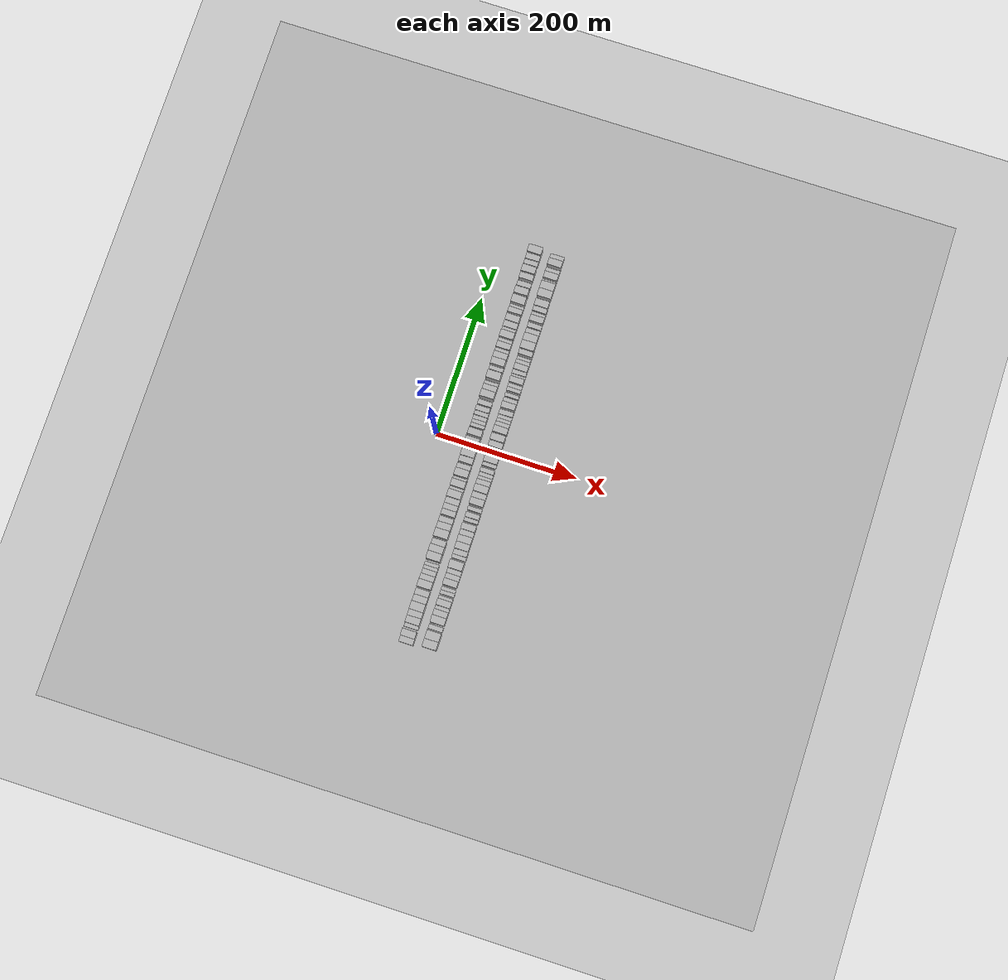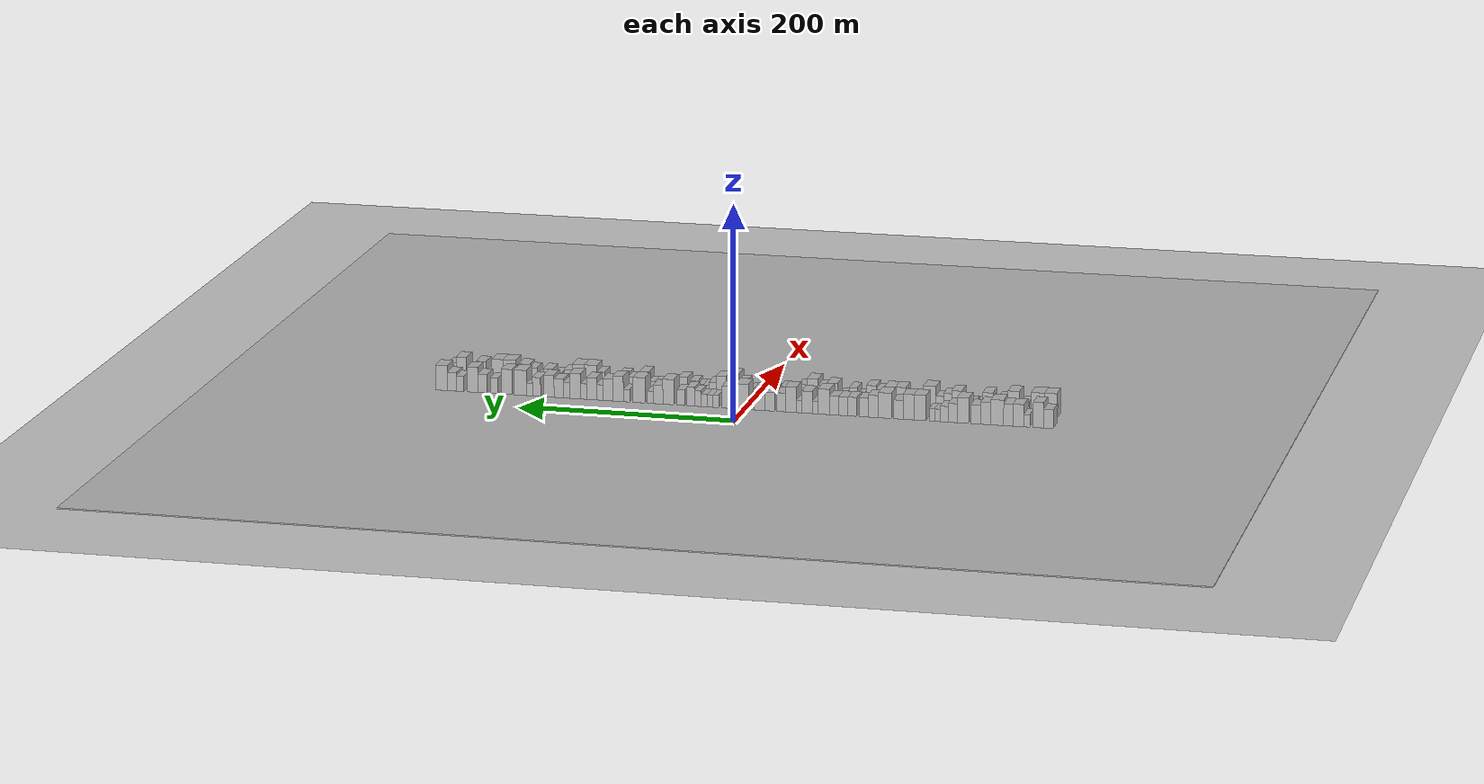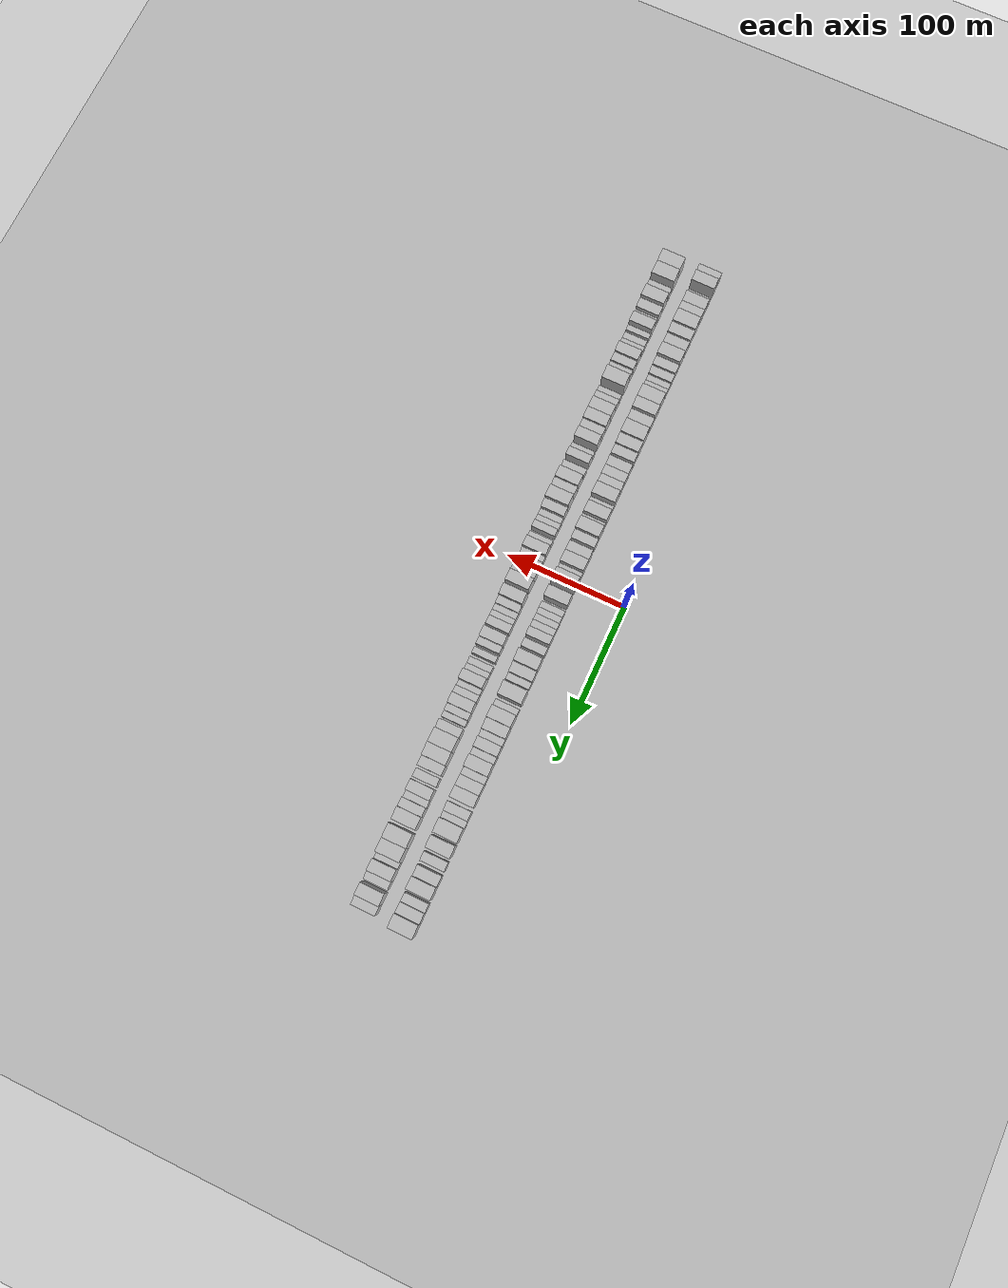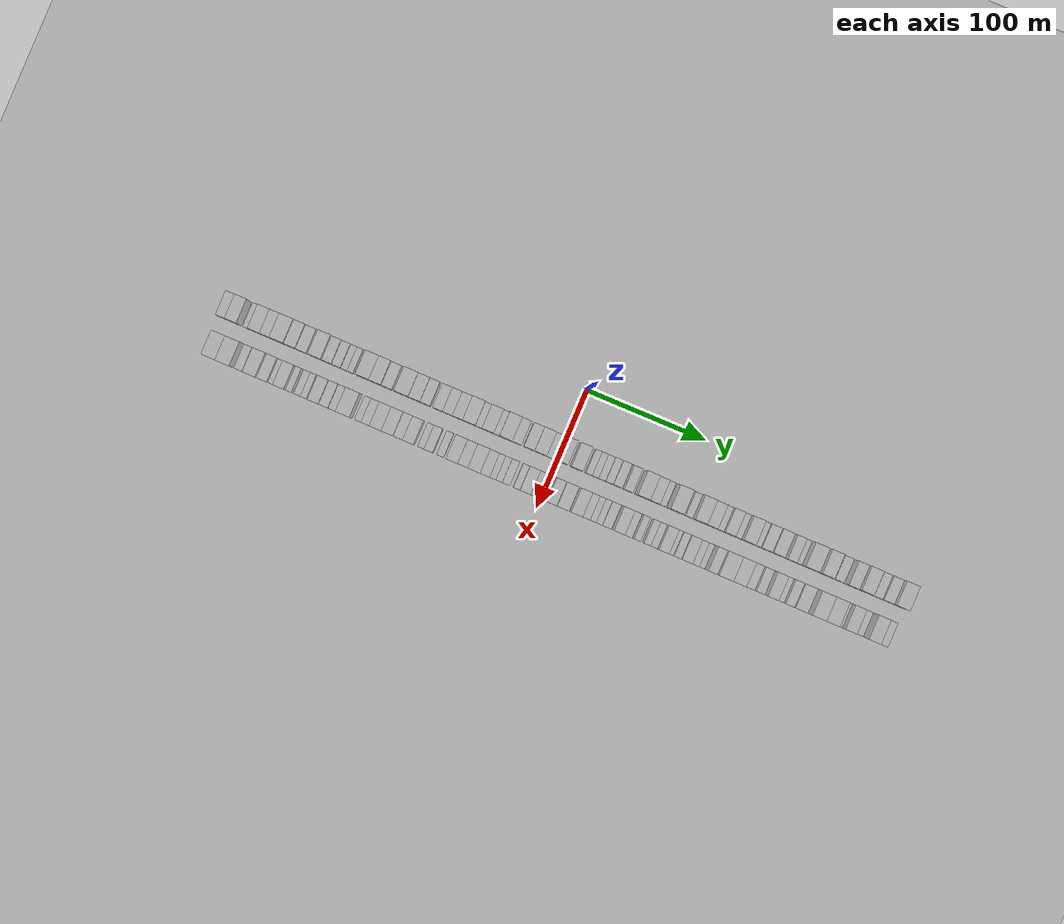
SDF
<?xml version="1.0" encoding="utf-8"?>

<sdf version="1.6">

   <world name="default">

      <gui fullscreen="0">

         <camera name="user_camera">

            <pose>-15 0 4.57585 0 0 0</pose>

            <view_controller>orbit</view_controller>

         </camera>

      </gui>

      <scene>

         <sky>

           <clouds>

             <speed>12</speed>

           </clouds>

         </sky>

         <ambient>0.4 0.4 0.4 1</ambient>

         <background>0.7 0.7 0.7 1</background>

         <shadows>1</shadows>

      </scene>

      <gravity>0 0 -9.8066</gravity>

      <magnetic_field>6e-06 2.3e-05 -4.2e-05</magnetic_field>

      <physics default="0" name="default_physics" type="ode">

         <ode>

            <solver>

               <type>quick</type>

               <iters>10</iters>

               <sor>1.0</sor>

               <use_dynamic_moi_rescaling>0</use_dynamic_moi_rescaling>

            </solver>

            <constraints>

               <cfm>0</cfm>

               <erp>0.2</erp>

               <contact_max_correcting_vel>100</contact_max_correcting_vel>

               <contact_surface_layer>0.001</contact_surface_layer>

            </constraints>

         </ode>

         <max_step_size>0.004</max_step_size>

         <real_time_factor>1</real_time_factor>

         <real_time_update_rate>250</real_time_update_rate>

      </physics>

      <light name="sun" type="directional">

         <cast_shadows>1</cast_shadows>

         <pose>0 0 10 0 0 0</pose>

         <diffuse>0.8 0.8 0.8 1</diffuse>

         <specular>0.2 0.2 0.2 1</specular>

         <attenuation>

            <range>1000</range>

            <constant>0.9</constant>

            <linear>0.01</linear>

            <quadratic>0.001</quadratic>

         </attenuation>

         <direction>-0.5 0.1 -0.9</direction>

      </light>

      <include>

         <name>ground_plane_1</name>

         <uri>model://HANNAS_ground_plane</uri>

         <pose>0 0 0  0 0 0</pose>

      </include>

      <include>

         <name>ground_plane_2</name>

         <uri>model://HANNAS_ground_plane</uri>

         <pose>100 0 0  0 0 0</pose>

      </include>

      <model name="building_1">

         <static>1</static>

         <pose frame="">50.0000 -279.6286 0 0.000000 0.000000 0.000000</pose>

         <link name="link">

            <pose frame="">0 0 9.00 0 0 0</pose>

            <collision name="collision">

               <geometry>

                  <box>

                     <size>20.0000 8.7428 18.0000</size>

                  </box>

               </geometry>

               <max_contacts>10</max_contacts>

               <surface>

                  <contact>

                     <ode/>

                  </contact>

                  <bounce/>

                  <friction>

                     <torsional>

                        <ode/>

                     </torsional>

                     <ode/>

                  </friction>

               </surface>

            </collision>

            <visual name="visual">

               <cast_shadows>0</cast_shadows>

               <geometry>

                  <box>

                     <size>20.0000 8.7428 18.0000</size>

                  </box>

               </geometry>

               <material>

                  <script>

                     <uri>model://HANNAS_wall/materials/scripts</uri>

                     <uri>model://HANNAS_wall/materials/textures</uri>

                     <name>vrc/HANNAS_wall</name>

                  </script>

               </material>

            </visual>

            <self_collide>0</self_collide>

            <enable_wind>0</enable_wind>

            <kinematic>0</kinematic>

         </link>

      </model>

      <model name="building_2">

         <static>1</static>

         <pose frame="">50.0000 -270.4098 0 0.000000 0.000000 0.000000</pose>

         <link name="link">

            <pose frame="">0 0 12.00 0 0 0</pose>

            <collision name="collision">

               <geometry>

                  <box>

                     <size>20.0000 9.6947 24.0000</size>

                  </box>

               </geometry>

               <max_contacts>10</max_contacts>

               <surface>

                  <contact>

                     <ode/>

                  </contact>

                  <bounce/>

                  <friction>

                     <torsional>

                        <ode/>

                     </torsional>

                     <ode/>

                  </friction>

               </surface>

            </collision>

            <visual name="visual">

               <cast_shadows>0</cast_shadows>

               <geometry>

                  <box>

                     <size>20.0000 9.6947 24.0000</size>

                  </box>

               </geometry>

               <material>

                  <script>

                     <uri>model://HANNAS_wall/materials/scripts</uri>

                     <uri>model://HANNAS_wall/materials/textures</uri>

                     <name>vrc/HANNAS_wall</name>

                  </script>

               </material>

            </visual>

            <self_collide>0</self_collide>

            <enable_wind>0</enable_wind>

            <kinematic>0</kinematic>

         </link>

      </model>

      <model name="building_3">

         <static>1</static>

         <pose frame="">50.0000 -259.7569 0 0.000000 0.000000 0.000000</pose>

         <link name="link">

            <pose frame="">0 0 6.00 0 0 0</pose>

            <collision name="collision">

               <geometry>

                  <box>

                     <size>20.0000 5.6109 12.0000</size>

                  </box>

               </geometry>

               <max_contacts>10</max_contacts>

               <surface>

                  <contact>

                     <ode/>

                  </contact>

                  <bounce/>

                  <friction>

                     <torsional>

                        <ode/>

                     </torsional>

                     <ode/>

                  </friction>

               </surface>

            </collision>

            <visual name="visual">

               <cast_shadows>0</cast_shadows>

               <geometry>

                  <box>

                     <size>20.0000 5.6109 12.0000</size>

                  </box>

               </geometry>

               <material>

                  <script>

                     <uri>model://HANNAS_wall/materials/scripts</uri>

                     <uri>model://HANNAS_wall/materials/textures</uri>

                     <name>vrc/HANNAS_wall</name>

                  </script>

               </material>

            </visual>

            <self_collide>0</self_collide>

            <enable_wind>0</enable_wind>

            <kinematic>0</kinematic>

         </link>

      </model>

      <model name="building_4">

         <static>1</static>

         <pose frame="">50.0000 -252.0025 0 0.000000 0.000000 0.000000</pose>

         <link name="link">

            <pose frame="">0 0 10.50 0 0 0</pose>

            <collision name="collision">

               <geometry>

                  <box>

                     <size>20.0000 9.8979 21.0000</size>

                  </box>

               </geometry>

               <max_contacts>10</max_contacts>

               <surface>

                  <contact>

                     <ode/>

                  </contact>

                  <bounce/>

                  <friction>

                     <torsional>

                        <ode/>

                     </torsional>

                     <ode/>

                  </friction>

               </surface>

            </collision>

            <visual name="visual">

               <cast_shadows>0</cast_shadows>

               <geometry>

                  <box>

                     <size>20.0000 9.8979 21.0000</size>

                  </box>

               </geometry>

               <material>

                  <script>

                     <uri>model://HANNAS_wall/materials/scripts</uri>

                     <uri>model://HANNAS_wall/materials/textures</uri>

                     <name>vrc/HANNAS_wall</name>

                  </script>

               </material>

            </visual>

            <self_collide>0</self_collide>

            <enable_wind>0</enable_wind>

            <kinematic>0</kinematic>

         </link>

      </model>

      <model name="building_5">

         <static>1</static>

         <pose frame="">50.0000 -242.8396 0 0.000000 0.000000 0.000000</pose>

         <link name="link">

            <pose frame="">0 0 10.50 0 0 0</pose>

            <collision name="collision">

               <geometry>

                  <box>

                     <size>20.0000 8.4280 21.0000</size>

                  </box>

               </geometry>

               <max_contacts>10</max_contacts>

               <surface>

                  <contact>

                     <ode/>

                  </contact>

                  <bounce/>

                  <friction>

                     <torsional>

                        <ode/>

                     </torsional>

                     <ode/>

                  </friction>

               </surface>

            </collision>

            <visual name="visual">

               <cast_shadows>0</cast_shadows>

               <geometry>

                  <box>

                     <size>20.0000 8.4280 21.0000</size>

                  </box>

               </geometry>

               <material>

                  <script>

                     <uri>model://HANNAS_wall/materials/scripts</uri>

                     <uri>model://HANNAS_wall/materials/textures</uri>

                     <name>vrc/HANNAS_wall</name>

                  </script>

               </material>

            </visual>

            <self_collide>0</self_collide>

            <enable_wind>0</enable_wind>

            <kinematic>0</kinematic>

         </link>

      </model>

      <model name="building_6">

         <static>1</static>

         <pose frame="">50.0000 -232.8476 0 0.000000 0.000000 0.000000</pose>

         <link name="link">

            <pose frame="">0 0 12.00 0 0 0</pose>

            <collision name="collision">

               <geometry>

                  <box>

                     <size>20.0000 11.5561 24.0000</size>

                  </box>

               </geometry>

               <max_contacts>10</max_contacts>

               <surface>

                  <contact>

                     <ode/>

                  </contact>

                  <bounce/>

                  <friction>

                     <torsional>

                        <ode/>

                     </torsional>

                     <ode/>

                  </friction>

               </surface>

            </collision>

            <visual name="visual">

               <cast_shadows>0</cast_shadows>

               <geometry>

                  <box>

                     <size>20.0000 11.5561 24.0000</size>

                  </box>

               </geometry>

               <material>

                  <script>

                     <uri>model://HANNAS_wall/materials/scripts</uri>

                     <uri>model://HANNAS_wall/materials/textures</uri>

                     <name>vrc/HANNAS_wall</name>

                  </script>

               </material>

            </visual>

            <self_collide>0</self_collide>

            <enable_wind>0</enable_wind>

            <kinematic>0</kinematic>

         </link>

      </model>

      <model name="building_7">

         <static>1</static>

         <pose frame="">50.0000 -222.4046 0 0.000000 0.000000 0.000000</pose>

         <link name="link">

            <pose frame="">0 0 10.50 0 0 0</pose>

            <collision name="collision">

               <geometry>

                  <box>

                     <size>20.0000 9.3298 21.0000</size>

                  </box>

               </geometry>

               <max_contacts>10</max_contacts>

               <surface>

                  <contact>

                     <ode/>

                  </contact>

                  <bounce/>

                  <friction>

                     <torsional>

                        <ode/>

                     </torsional>

                     <ode/>

                  </friction>

               </surface>

            </collision>

            <visual name="visual">

               <cast_shadows>0</cast_shadows>

               <geometry>

                  <box>

                     <size>20.0000 9.3298 21.0000</size>

                  </box>

               </geometry>

               <material>

                  <script>

                     <uri>model://HANNAS_wall/materials/scripts</uri>

                     <uri>model://HANNAS_wall/materials/textures</uri>

                     <name>vrc/HANNAS_wall</name>

                  </script>

               </material>

            </visual>

            <self_collide>0</self_collide>

            <enable_wind>0</enable_wind>

            <kinematic>0</kinematic>

         </link>

      </model>

      <model name="building_8">

         <static>1</static>

         <pose frame="">50.0000 -213.2914 0 0.000000 0.000000 0.000000</pose>

         <link name="link">

            <pose frame="">0 0 9.00 0 0 0</pose>

            <collision name="collision">

               <geometry>

                  <box>

                     <size>20.0000 8.8967 18.0000</size>

                  </box>

               </geometry>

               <max_contacts>10</max_contacts>

               <surface>

                  <contact>

                     <ode/>

                  </contact>

                  <bounce/>

                  <friction>

                     <torsional>

                        <ode/>

                     </torsional>

                     <ode/>

                  </friction>

               </surface>

            </collision>

            <visual name="visual">

               <cast_shadows>0</cast_shadows>

               <geometry>

                  <box>

                     <size>20.0000 8.8967 18.0000</size>

                  </box>

               </geometry>

               <material>

                  <script>

                     <uri>model://HANNAS_wall/materials/scripts</uri>

                     <uri>model://HANNAS_wall/materials/textures</uri>

                     <name>vrc/HANNAS_wall</name>

                  </script>

               </material>

            </visual>

            <self_collide>0</self_collide>

            <enable_wind>0</enable_wind>

            <kinematic>0</kinematic>

         </link>

      </model>

      <model name="building_9">

         <static>1</static>

         <pose frame="">50.0000 -201.5063 0 0.000000 0.000000 0.000000</pose>

         <link name="link">

            <pose frame="">0 0 12.00 0 0 0</pose>

            <collision name="collision">

               <geometry>

                  <box>

                     <size>20.0000 10.6734 24.0000</size>

                  </box>

               </geometry>

               <max_contacts>10</max_contacts>

               <surface>

                  <contact>

                     <ode/>

                  </contact>

                  <bounce/>

                  <friction>

                     <torsional>

                        <ode/>

                     </torsional>

                     <ode/>

                  </friction>

               </surface>

            </collision>

            <visual name="visual">

               <cast_shadows>0</cast_shadows>

               <geometry>

                  <box>

                     <size>20.0000 10.6734 24.0000</size>

                  </box>

               </geometry>

               <material>

                  <script>

                     <uri>model://HANNAS_wall/materials/scripts</uri>

                     <uri>model://HANNAS_wall/materials/textures</uri>

                     <name>vrc/HANNAS_wall</name>

                  </script>

               </material>

            </visual>

            <self_collide>0</self_collide>

            <enable_wind>0</enable_wind>

            <kinematic>0</kinematic>

         </link>

      </model>

      <model name="building_10">

         <static>1</static>

         <pose frame="">50.0000 -192.1429 0 0.000000 0.000000 0.000000</pose>

         <link name="link">

            <pose frame="">0 0 9.00 0 0 0</pose>

            <collision name="collision">

               <geometry>

                  <box>

                     <size>20.0000 8.0535 18.0000</size>

                  </box>

               </geometry>

               <max_contacts>10</max_contacts>

               <surface>

                  <contact>

                     <ode/>

                  </contact>

                  <bounce/>

                  <friction>

                     <torsional>

                        <ode/>

                     </torsional>

                     <ode/>

                  </friction>

               </surface>

            </collision>

            <visual name="visual">

               <cast_shadows>0</cast_shadows>

               <geometry>

                  <box>

                     <size>20.0000 8.0535 18.0000</size>

                  </box>

               </geometry>

               <material>

                  <script>

                     <uri>model://HANNAS_wall/materials/scripts</uri>

                     <uri>model://HANNAS_wall/materials/textures</uri>

                     <name>vrc/HANNAS_wall</name>

                  </script>

               </material>

            </visual>

            <self_collide>0</self_collide>

            <enable_wind>0</enable_wind>

            <kinematic>0</kinematic>

         </link>

      </model>

      <model name="building_11">

         <static>1</static>

         <pose frame="">50.0000 -184.4632 0 0.000000 0.000000 0.000000</pose>

         <link name="link">

            <pose frame="">0 0 7.50 0 0 0</pose>

            <collision name="collision">

               <geometry>

                  <box>

                     <size>20.0000 7.3059 15.0000</size>

                  </box>

               </geometry>

               <max_contacts>10</max_contacts>

               <surface>

                  <contact>

                     <ode/>

                  </contact>

                  <bounce/>

                  <friction>

                     <torsional>

                        <ode/>

                     </torsional>

                     <ode/>

                  </friction>

               </surface>

            </collision>

            <visual name="visual">

               <cast_shadows>0</cast_shadows>

               <geometry>

                  <box>

                     <size>20.0000 7.3059 15.0000</size>

                  </box>

               </geometry>

               <material>

                  <script>

                     <uri>model://HANNAS_wall/materials/scripts</uri>

                     <uri>model://HANNAS_wall/materials/textures</uri>

                     <name>vrc/HANNAS_wall</name>

                  </script>

               </material>

            </visual>

            <self_collide>0</self_collide>

            <enable_wind>0</enable_wind>

            <kinematic>0</kinematic>

         </link>

      </model>

      <model name="building_12">

         <static>1</static>

         <pose frame="">50.0000 -178.2187 0 0.000000 0.000000 0.000000</pose>

         <link name="link">

            <pose frame="">0 0 6.00 0 0 0</pose>

            <collision name="collision">

               <geometry>

                  <box>

                     <size>20.0000 5.1832 12.0000</size>

                  </box>

               </geometry>

               <max_contacts>10</max_contacts>

               <surface>

                  <contact>

                     <ode/>

                  </contact>

                  <bounce/>

                  <friction>

                     <torsional>

                        <ode/>

                     </torsional>

                     <ode/>

                  </friction>

               </surface>

            </collision>

            <visual name="visual">

               <cast_shadows>0</cast_shadows>

               <geometry>

                  <box>

                     <size>20.0000 5.1832 12.0000</size>

                  </box>

               </geometry>

               <material>

                  <script>

                     <uri>model://HANNAS_wall/materials/scripts</uri>

                     <uri>model://HANNAS_wall/materials/textures</uri>

                     <name>vrc/HANNAS_wall</name>

                  </script>

               </material>

            </visual>

            <self_collide>0</self_collide>

            <enable_wind>0</enable_wind>

            <kinematic>0</kinematic>

         </link>

      </model>

      <model name="building_13">

         <static>1</static>

         <pose frame="">50.0000 -173.1436 0 0.000000 0.000000 0.000000</pose>

         <link name="link">

            <pose frame="">0 0 6.00 0 0 0</pose>

            <collision name="collision">

               <geometry>

                  <box>

                     <size>20.0000 4.9670 12.0000</size>

                  </box>

               </geometry>

               <max_contacts>10</max_contacts>

               <surface>

                  <contact>

                     <ode/>

                  </contact>

                  <bounce/>

                  <friction>

                     <torsional>

                        <ode/>

                     </torsional>

                     <ode/>

                  </friction>

               </surface>

            </collision>

            <visual name="visual">

               <cast_shadows>0</cast_shadows>

               <geometry>

                  <box>

                     <size>20.0000 4.9670 12.0000</size>

                  </box>

               </geometry>

               <material>

                  <script>

                     <uri>model://HANNAS_wall/materials/scripts</uri>

                     <uri>model://HANNAS_wall/materials/textures</uri>

                     <name>vrc/HANNAS_wall</name>

                  </script>

               </material>

            </visual>

            <self_collide>0</self_collide>

            <enable_wind>0</enable_wind>

            <kinematic>0</kinematic>

         </link>

      </model>

      <model name="building_14">

         <static>1</static>

         <pose frame="">50.0000 -162.1004 0 0.000000 0.000000 0.000000</pose>

         <link name="link">

            <pose frame="">0 0 12.00 0 0 0</pose>

            <collision name="collision">

               <geometry>

                  <box>

                     <size>20.0000 11.1194 24.0000</size>

                  </box>

               </geometry>

               <max_contacts>10</max_contacts>

               <surface>

                  <contact>

                     <ode/>

                  </contact>

                  <bounce/>

                  <friction>

                     <torsional>

                        <ode/>

                     </torsional>

                     <ode/>

                  </friction>

               </surface>

            </collision>

            <visual name="visual">

               <cast_shadows>0</cast_shadows>

               <geometry>

                  <box>

                     <size>20.0000 11.1194 24.0000</size>

                  </box>

               </geometry>

               <material>

                  <script>

                     <uri>model://HANNAS_wall/materials/scripts</uri>

                     <uri>model://HANNAS_wall/materials/textures</uri>

                     <name>vrc/HANNAS_wall</name>

                  </script>

               </material>

            </visual>

            <self_collide>0</self_collide>

            <enable_wind>0</enable_wind>

            <kinematic>0</kinematic>

         </link>

      </model>

      <model name="building_15">

         <static>1</static>

         <pose frame="">50.0000 -151.5763 0 0.000000 0.000000 0.000000</pose>

         <link name="link">

            <pose frame="">0 0 12.00 0 0 0</pose>

            <collision name="collision">

               <geometry>

                  <box>

                     <size>20.0000 9.9287 24.0000</size>

                  </box>

               </geometry>

               <max_contacts>10</max_contacts>

               <surface>

                  <contact>

                     <ode/>

                  </contact>

                  <bounce/>

                  <friction>

                     <torsional>

                        <ode/>

                     </torsional>

                     <ode/>

                  </friction>

               </surface>

            </collision>

            <visual name="visual">

               <cast_shadows>0</cast_shadows>

               <geometry>

                  <box>

                     <size>20.0000 9.9287 24.0000</size>

                  </box>

               </geometry>

               <material>

                  <script>

                     <uri>model://HANNAS_wall/materials/scripts</uri>

                     <uri>model://HANNAS_wall/materials/textures</uri>

                     <name>vrc/HANNAS_wall</name>

                  </script>

               </material>

            </visual>

            <self_collide>0</self_collide>

            <enable_wind>0</enable_wind>

            <kinematic>0</kinematic>

         </link>

      </model>

      <model name="building_16">

         <static>1</static>

         <pose frame="">50.0000 -142.2535 0 0.000000 0.000000 0.000000</pose>

         <link name="link">

            <pose frame="">0 0 9.00 0 0 0</pose>

            <collision name="collision">

               <geometry>

                  <box>

                     <size>20.0000 8.7169 18.0000</size>

                  </box>

               </geometry>

               <max_contacts>10</max_contacts>

               <surface>

                  <contact>

                     <ode/>

                  </contact>

                  <bounce/>

                  <friction>

                     <torsional>

                        <ode/>

                     </torsional>

                     <ode/>

                  </friction>

               </surface>

            </collision>

            <visual name="visual">

               <cast_shadows>0</cast_shadows>

               <geometry>

                  <box>

                     <size>20.0000 8.7169 18.0000</size>

                  </box>

               </geometry>

               <material>

                  <script>

                     <uri>model://HANNAS_wall/materials/scripts</uri>

                     <uri>model://HANNAS_wall/materials/textures</uri>

                     <name>vrc/HANNAS_wall</name>

                  </script>

               </material>

            </visual>

            <self_collide>0</self_collide>

            <enable_wind>0</enable_wind>

            <kinematic>0</kinematic>

         </link>

      </model>

      <model name="building_17">

         <static>1</static>

         <pose frame="">50.0000 -129.9366 0 0.000000 0.000000 0.000000</pose>

         <link name="link">

            <pose frame="">0 0 12.00 0 0 0</pose>

            <collision name="collision">

               <geometry>

                  <box>

                     <size>20.0000 11.9170 24.0000</size>

                  </box>

               </geometry>

               <max_contacts>10</max_contacts>

               <surface>

                  <contact>

                     <ode/>

                  </contact>

                  <bounce/>

                  <friction>

                     <torsional>

                        <ode/>

                     </torsional>

                     <ode/>

                  </friction>

               </surface>

            </collision>

            <visual name="visual">

               <cast_shadows>0</cast_shadows>

               <geometry>

                  <box>

                     <size>20.0000 11.9170 24.0000</size>

                  </box>

               </geometry>

               <material>

                  <script>

                     <uri>model://HANNAS_wall/materials/scripts</uri>

                     <uri>model://HANNAS_wall/materials/textures</uri>

                     <name>vrc/HANNAS_wall</name>

                  </script>

               </material>

            </visual>

            <self_collide>0</self_collide>

            <enable_wind>0</enable_wind>

            <kinematic>0</kinematic>

         </link>

      </model>

      <model name="building_18">

         <static>1</static>

         <pose frame="">50.0000 -119.2234 0 0.000000 0.000000 0.000000</pose>

         <link name="link">

            <pose frame="">0 0 10.50 0 0 0</pose>

            <collision name="collision">

               <geometry>

                  <box>

                     <size>20.0000 9.5093 21.0000</size>

                  </box>

               </geometry>

               <max_contacts>10</max_contacts>

               <surface>

                  <contact>

                     <ode/>

                  </contact>

                  <bounce/>

                  <friction>

                     <torsional>

                        <ode/>

                     </torsional>

                     <ode/>

                  </friction>

               </surface>

            </collision>

            <visual name="visual">

               <cast_shadows>0</cast_shadows>

               <geometry>

                  <box>

                     <size>20.0000 9.5093 21.0000</size>

                  </box>

               </geometry>

               <material>

                  <script>

                     <uri>model://HANNAS_wall/materials/scripts</uri>

                     <uri>model://HANNAS_wall/materials/textures</uri>

                     <name>vrc/HANNAS_wall</name>

                  </script>

               </material>

            </visual>

            <self_collide>0</self_collide>

            <enable_wind>0</enable_wind>

            <kinematic>0</kinematic>

         </link>

      </model>

      <model name="building_19">

         <static>1</static>

         <pose frame="">50.0000 -110.3324 0 0.000000 0.000000 0.000000</pose>

         <link name="link">

            <pose frame="">0 0 9.00 0 0 0</pose>

            <collision name="collision">

               <geometry>

                  <box>

                     <size>20.0000 8.2729 18.0000</size>

                  </box>

               </geometry>

               <max_contacts>10</max_contacts>

               <surface>

                  <contact>

                     <ode/>

                  </contact>

                  <bounce/>

                  <friction>

                     <torsional>

                        <ode/>

                     </torsional>

                     <ode/>

                  </friction>

               </surface>

            </collision>

            <visual name="visual">

               <cast_shadows>0</cast_shadows>

               <geometry>

                  <box>

                     <size>20.0000 8.2729 18.0000</size>

                  </box>

               </geometry>

               <material>

                  <script>

                     <uri>model://HANNAS_wall/materials/scripts</uri>

                     <uri>model://HANNAS_wall/materials/textures</uri>

                     <name>vrc/HANNAS_wall</name>

                  </script>

               </material>

            </visual>

            <self_collide>0</self_collide>

            <enable_wind>0</enable_wind>

            <kinematic>0</kinematic>

         </link>

      </model>

      <model name="building_20">

         <static>1</static>

         <pose frame="">50.0000 -100.0319 0 0.000000 0.000000 0.000000</pose>

         <link name="link">

            <pose frame="">0 0 9.00 0 0 0</pose>

            <collision name="collision">

               <geometry>

                  <box>

                     <size>20.0000 8.3281 18.0000</size>

                  </box>

               </geometry>

               <max_contacts>10</max_contacts>

               <surface>

                  <contact>

                     <ode/>

                  </contact>

                  <bounce/>

                  <friction>

                     <torsional>

                        <ode/>

                     </torsional>

                     <ode/>

                  </friction>

               </surface>

            </collision>

            <visual name="visual">

               <cast_shadows>0</cast_shadows>

               <geometry>

                  <box>

                     <size>20.0000 8.3281 18.0000</size>

                  </box>

               </geometry>

               <material>

                  <script>

                     <uri>model://HANNAS_wall/materials/scripts</uri>

                     <uri>model://HANNAS_wall/materials/textures</uri>

                     <name>vrc/HANNAS_wall</name>

                  </script>

               </material>

            </visual>

            <self_collide>0</self_collide>

            <enable_wind>0</enable_wind>

            <kinematic>0</kinematic>

         </link>

      </model>

      <model name="building_21">

         <static>1</static>

         <pose frame="">50.0000 -91.8018 0 0.000000 0.000000 0.000000</pose>

         <link name="link">

            <pose frame="">0 0 9.00 0 0 0</pose>

            <collision name="collision">

               <geometry>

                  <box>

                     <size>20.0000 8.1321 18.0000</size>

                  </box>

               </geometry>

               <max_contacts>10</max_contacts>

               <surface>

                  <contact>

                     <ode/>

                  </contact>

                  <bounce/>

                  <friction>

                     <torsional>

                        <ode/>

                     </torsional>

                     <ode/>

                  </friction>

               </surface>

            </collision>

            <visual name="visual">

               <cast_shadows>0</cast_shadows>

               <geometry>

                  <box>

                     <size>20.0000 8.1321 18.0000</size>

                  </box>

               </geometry>

               <material>

                  <script>

                     <uri>model://HANNAS_wall/materials/scripts</uri>

                     <uri>model://HANNAS_wall/materials/textures</uri>

                     <name>vrc/HANNAS_wall</name>

                  </script>

               </material>

            </visual>

            <self_collide>0</self_collide>

            <enable_wind>0</enable_wind>

            <kinematic>0</kinematic>

         </link>

      </model>

      <model name="building_22">

         <static>1</static>

         <pose frame="">50.0000 -83.4496 0 0.000000 0.000000 0.000000</pose>

         <link name="link">

            <pose frame="">0 0 9.00 0 0 0</pose>

            <collision name="collision">

               <geometry>

                  <box>

                     <size>20.0000 8.5723 18.0000</size>

                  </box>

               </geometry>

               <max_contacts>10</max_contacts>

               <surface>

                  <contact>

                     <ode/>

                  </contact>

                  <bounce/>

                  <friction>

                     <torsional>

                        <ode/>

                     </torsional>

                     <ode/>

                  </friction>

               </surface>

            </collision>

            <visual name="visual">

               <cast_shadows>0</cast_shadows>

               <geometry>

                  <box>

                     <size>20.0000 8.5723 18.0000</size>

                  </box>

               </geometry>

               <material>

                  <script>

                     <uri>model://HANNAS_wall/materials/scripts</uri>

                     <uri>model://HANNAS_wall/materials/textures</uri>

                     <name>vrc/HANNAS_wall</name>

                  </script>

               </material>

            </visual>

            <self_collide>0</self_collide>

            <enable_wind>0</enable_wind>

            <kinematic>0</kinematic>

         </link>

      </model>

      <model name="building_23">

         <static>1</static>

         <pose frame="">50.0000 -73.8428 0 0.000000 0.000000 0.000000</pose>

         <link name="link">

            <pose frame="">0 0 12.00 0 0 0</pose>

            <collision name="collision">

               <geometry>

                  <box>

                     <size>20.0000 10.6414 24.0000</size>

                  </box>

               </geometry>

               <max_contacts>10</max_contacts>

               <surface>

                  <contact>

                     <ode/>

                  </contact>

                  <bounce/>

                  <friction>

                     <torsional>

                        <ode/>

                     </torsional>

                     <ode/>

                  </friction>

               </surface>

            </collision>

            <visual name="visual">

               <cast_shadows>0</cast_shadows>

               <geometry>

                  <box>

                     <size>20.0000 10.6414 24.0000</size>

                  </box>

               </geometry>

               <material>

                  <script>

                     <uri>model://HANNAS_wall/materials/scripts</uri>

                     <uri>model://HANNAS_wall/materials/textures</uri>

                     <name>vrc/HANNAS_wall</name>

                  </script>

               </material>

            </visual>

            <self_collide>0</self_collide>

            <enable_wind>0</enable_wind>

            <kinematic>0</kinematic>

         </link>

      </model>

      <model name="building_24">

         <static>1</static>

         <pose frame="">50.0000 -65.8612 0 0.000000 0.000000 0.000000</pose>

         <link name="link">

            <pose frame="">0 0 6.00 0 0 0</pose>

            <collision name="collision">

               <geometry>

                  <box>

                     <size>20.0000 5.3218 12.0000</size>

                  </box>

               </geometry>

               <max_contacts>10</max_contacts>

               <surface>

                  <contact>

                     <ode/>

                  </contact>

                  <bounce/>

                  <friction>

                     <torsional>

                        <ode/>

                     </torsional>

                     <ode/>

                  </friction>

               </surface>

            </collision>

            <visual name="visual">

               <cast_shadows>0</cast_shadows>

               <geometry>

                  <box>

                     <size>20.0000 5.3218 12.0000</size>

                  </box>

               </geometry>

               <material>

                  <script>

                     <uri>model://HANNAS_wall/materials/scripts</uri>

                     <uri>model://HANNAS_wall/materials/textures</uri>

                     <name>vrc/HANNAS_wall</name>

                  </script>

               </material>

            </visual>

            <self_collide>0</self_collide>

            <enable_wind>0</enable_wind>

            <kinematic>0</kinematic>

         </link>

      </model>

      <model name="building_25">

         <static>1</static>

         <pose frame="">50.0000 -58.2355 0 0.000000 0.000000 0.000000</pose>

         <link name="link">

            <pose frame="">0 0 10.50 0 0 0</pose>

            <collision name="collision">

               <geometry>

                  <box>

                     <size>20.0000 9.9295 21.0000</size>

                  </box>

               </geometry>

               <max_contacts>10</max_contacts>

               <surface>

                  <contact>

                     <ode/>

                  </contact>

                  <bounce/>

                  <friction>

                     <torsional>

                        <ode/>

                     </torsional>

                     <ode/>

                  </friction>

               </surface>

            </collision>

            <visual name="visual">

               <cast_shadows>0</cast_shadows>

               <geometry>

                  <box>

                     <size>20.0000 9.9295 21.0000</size>

                  </box>

               </geometry>

               <material>

                  <script>

                     <uri>model://HANNAS_wall/materials/scripts</uri>

                     <uri>model://HANNAS_wall/materials/textures</uri>

                     <name>vrc/HANNAS_wall</name>

                  </script>

               </material>

            </visual>

            <self_collide>0</self_collide>

            <enable_wind>0</enable_wind>

            <kinematic>0</kinematic>

         </link>

      </model>

      <model name="building_26">

         <static>1</static>

         <pose frame="">50.0000 -50.8598 0 0.000000 0.000000 0.000000</pose>

         <link name="link">

            <pose frame="">0 0 6.00 0 0 0</pose>

            <collision name="collision">

               <geometry>

                  <box>

                     <size>20.0000 4.8219 12.0000</size>

                  </box>

               </geometry>

               <max_contacts>10</max_contacts>

               <surface>

                  <contact>

                     <ode/>

                  </contact>

                  <bounce/>

                  <friction>

                     <torsional>

                        <ode/>

                     </torsional>

                     <ode/>

                  </friction>

               </surface>

            </collision>

            <visual name="visual">

               <cast_shadows>0</cast_shadows>

               <geometry>

                  <box>

                     <size>20.0000 4.8219 12.0000</size>

                  </box>

               </geometry>

               <material>

                  <script>

                     <uri>model://HANNAS_wall/materials/scripts</uri>

                     <uri>model://HANNAS_wall/materials/textures</uri>

                     <name>vrc/HANNAS_wall</name>

                  </script>

               </material>

            </visual>

            <self_collide>0</self_collide>

            <enable_wind>0</enable_wind>

            <kinematic>0</kinematic>

         </link>

      </model>

      <model name="building_27">

         <static>1</static>

         <pose frame="">50.0000 -43.2296 0 0.000000 0.000000 0.000000</pose>

         <link name="link">

            <pose frame="">0 0 12.00 0 0 0</pose>

            <collision name="collision">

               <geometry>

                  <box>

                     <size>20.0000 10.4385 24.0000</size>

                  </box>

               </geometry>

               <max_contacts>10</max_contacts>

               <surface>

                  <contact>

                     <ode/>

                  </contact>

                  <bounce/>

                  <friction>

                     <torsional>

                        <ode/>

                     </torsional>

                     <ode/>

                  </friction>

               </surface>

            </collision>

            <visual name="visual">

               <cast_shadows>0</cast_shadows>

               <geometry>

                  <box>

                     <size>20.0000 10.4385 24.0000</size>

                  </box>

               </geometry>

               <material>

                  <script>

                     <uri>model://HANNAS_wall/materials/scripts</uri>

                     <uri>model://HANNAS_wall/materials/textures</uri>

                     <name>vrc/HANNAS_wall</name>

                  </script>

               </material>

            </visual>

            <self_collide>0</self_collide>

            <enable_wind>0</enable_wind>

            <kinematic>0</kinematic>

         </link>

      </model>

      <model name="building_28">

         <static>1</static>

         <pose frame="">50.0000 -34.0808 0 0.000000 0.000000 0.000000</pose>

         <link name="link">

            <pose frame="">0 0 9.00 0 0 0</pose>

            <collision name="collision">

               <geometry>

                  <box>

                     <size>20.0000 7.8592 18.0000</size>

                  </box>

               </geometry>

               <max_contacts>10</max_contacts>

               <surface>

                  <contact>

                     <ode/>

                  </contact>

                  <bounce/>

                  <friction>

                     <torsional>

                        <ode/>

                     </torsional>

                     <ode/>

                  </friction>

               </surface>

            </collision>

            <visual name="visual">

               <cast_shadows>0</cast_shadows>

               <geometry>

                  <box>

                     <size>20.0000 7.8592 18.0000</size>

                  </box>

               </geometry>

               <material>

                  <script>

                     <uri>model://HANNAS_wall/materials/scripts</uri>

                     <uri>model://HANNAS_wall/materials/textures</uri>

                     <name>vrc/HANNAS_wall</name>

                  </script>

               </material>

            </visual>

            <self_collide>0</self_collide>

            <enable_wind>0</enable_wind>

            <kinematic>0</kinematic>

         </link>

      </model>

      <model name="building_29">

         <static>1</static>

         <pose frame="">50.0000 -23.7560 0 0.000000 0.000000 0.000000</pose>

         <link name="link">

            <pose frame="">0 0 9.00 0 0 0</pose>

            <collision name="collision">

               <geometry>

                  <box>

                     <size>20.0000 8.7904 18.0000</size>

                  </box>

               </geometry>

               <max_contacts>10</max_contacts>

               <surface>

                  <contact>

                     <ode/>

                  </contact>

                  <bounce/>

                  <friction>

                     <torsional>

                        <ode/>

                     </torsional>

                     <ode/>

                  </friction>

               </surface>

            </collision>

            <visual name="visual">

               <cast_shadows>0</cast_shadows>

               <geometry>

                  <box>

                     <size>20.0000 8.7904 18.0000</size>

                  </box>

               </geometry>

               <material>

                  <script>

                     <uri>model://HANNAS_wall/materials/scripts</uri>

                     <uri>model://HANNAS_wall/materials/textures</uri>

                     <name>vrc/HANNAS_wall</name>

                  </script>

               </material>

            </visual>

            <self_collide>0</self_collide>

            <enable_wind>0</enable_wind>

            <kinematic>0</kinematic>

         </link>

      </model>

      <model name="building_30">

         <static>1</static>

         <pose frame="">50.0000 -14.3953 0 0.000000 0.000000 0.000000</pose>

         <link name="link">

            <pose frame="">0 0 10.50 0 0 0</pose>

            <collision name="collision">

               <geometry>

                  <box>

                     <size>20.0000 9.9312 21.0000</size>

                  </box>

               </geometry>

               <max_contacts>10</max_contacts>

               <surface>

                  <contact>

                     <ode/>

                  </contact>

                  <bounce/>

                  <friction>

                     <torsional>

                        <ode/>

                     </torsional>

                     <ode/>

                  </friction>

               </surface>

            </collision>

            <visual name="visual">

               <cast_shadows>0</cast_shadows>

               <geometry>

                  <box>

                     <size>20.0000 9.9312 21.0000</size>

                  </box>

               </geometry>

               <material>

                  <script>

                     <uri>model://HANNAS_wall/materials/scripts</uri>

                     <uri>model://HANNAS_wall/materials/textures</uri>

                     <name>vrc/HANNAS_wall</name>

                  </script>

               </material>

            </visual>

            <self_collide>0</self_collide>

            <enable_wind>0</enable_wind>

            <kinematic>0</kinematic>

         </link>

      </model>

      <model name="building_31">

         <static>1</static>

         <pose frame="">50.0000 -6.5884 0 0.000000 0.000000 0.000000</pose>

         <link name="link">

            <pose frame="">0 0 6.00 0 0 0</pose>

            <collision name="collision">

               <geometry>

                  <box>

                     <size>20.0000 5.6824 12.0000</size>

                  </box>

               </geometry>

               <max_contacts>10</max_contacts>

               <surface>

                  <contact>

                     <ode/>

                  </contact>

                  <bounce/>

                  <friction>

                     <torsional>

                        <ode/>

                     </torsional>

                     <ode/>

                  </friction>

               </surface>

            </collision>

            <visual name="visual">

               <cast_shadows>0</cast_shadows>

               <geometry>

                  <box>

                     <size>20.0000 5.6824 12.0000</size>

                  </box>

               </geometry>

               <material>

                  <script>

                     <uri>model://HANNAS_wall/materials/scripts</uri>

                     <uri>model://HANNAS_wall/materials/textures</uri>

                     <name>vrc/HANNAS_wall</name>

                  </script>

               </material>

            </visual>

            <self_collide>0</self_collide>

            <enable_wind>0</enable_wind>

            <kinematic>0</kinematic>

         </link>

      </model>

      <model name="building_32">

         <static>1</static>

         <pose frame="">50.0000 2.1094 0 0.000000 0.000000 0.000000</pose>

         <link name="link">

            <pose frame="">0 0 12.00 0 0 0</pose>

            <collision name="collision">

               <geometry>

                  <box>

                     <size>20.0000 11.7132 24.0000</size>

                  </box>

               </geometry>

               <max_contacts>10</max_contacts>

               <surface>

                  <contact>

                     <ode/>

                  </contact>

                  <bounce/>

                  <friction>

                     <torsional>

                        <ode/>

                     </torsional>

                     <ode/>

                  </friction>

               </surface>

            </collision>

            <visual name="visual">

               <cast_shadows>0</cast_shadows>

               <geometry>

                  <box>

                     <size>20.0000 11.7132 24.0000</size>

                  </box>

               </geometry>

               <material>

                  <script>

                     <uri>model://HANNAS_wall/materials/scripts</uri>

                     <uri>model://HANNAS_wall/materials/textures</uri>

                     <name>vrc/HANNAS_wall</name>

                  </script>

               </material>

            </visual>

            <self_collide>0</self_collide>

            <enable_wind>0</enable_wind>

            <kinematic>0</kinematic>

         </link>

      </model>

      <model name="building_33">

         <static>1</static>

         <pose frame="">50.0000 15.8204 0 0.000000 0.000000 0.000000</pose>

         <link name="link">

            <pose frame="">0 0 10.50 0 0 0</pose>

            <collision name="collision">

               <geometry>

                  <box>

                     <size>20.0000 9.7087 21.0000</size>

                  </box>

               </geometry>

               <max_contacts>10</max_contacts>

               <surface>

                  <contact>

                     <ode/>

                  </contact>

                  <bounce/>

                  <friction>

                     <torsional>

                        <ode/>

                     </torsional>

                     <ode/>

                  </friction>

               </surface>

            </collision>

            <visual name="visual">

               <cast_shadows>0</cast_shadows>

               <geometry>

                  <box>

                     <size>20.0000 9.7087 21.0000</size>

                  </box>

               </geometry>

               <material>

                  <script>

                     <uri>model://HANNAS_wall/materials/scripts</uri>

                     <uri>model://HANNAS_wall/materials/textures</uri>

                     <name>vrc/HANNAS_wall</name>

                  </script>

               </material>

            </visual>

            <self_collide>0</self_collide>

            <enable_wind>0</enable_wind>

            <kinematic>0</kinematic>

         </link>

      </model>

      <model name="building_34">

         <static>1</static>

         <pose frame="">50.0000 26.3142 0 0.000000 0.000000 0.000000</pose>

         <link name="link">

            <pose frame="">0 0 6.00 0 0 0</pose>

            <collision name="collision">

               <geometry>

                  <box>

                     <size>20.0000 5.2790 12.0000</size>

                  </box>

               </geometry>

               <max_contacts>10</max_contacts>

               <surface>

                  <contact>

                     <ode/>

                  </contact>

                  <bounce/>

                  <friction>

                     <torsional>

                        <ode/>

                     </torsional>

                     <ode/>

                  </friction>

               </surface>

            </collision>

            <visual name="visual">

               <cast_shadows>0</cast_shadows>

               <geometry>

                  <box>

                     <size>20.0000 5.2790 12.0000</size>

                  </box>

               </geometry>

               <material>

                  <script>

                     <uri>model://HANNAS_wall/materials/scripts</uri>

                     <uri>model://HANNAS_wall/materials/textures</uri>

                     <name>vrc/HANNAS_wall</name>

                  </script>

               </material>

            </visual>

            <self_collide>0</self_collide>

            <enable_wind>0</enable_wind>

            <kinematic>0</kinematic>

         </link>

      </model>

      <model name="building_35">

         <static>1</static>

         <pose frame="">50.0000 31.6082 0 0.000000 0.000000 0.000000</pose>

         <link name="link">

            <pose frame="">0 0 6.00 0 0 0</pose>

            <collision name="collision">

               <geometry>

                  <box>

                     <size>20.0000 5.3090 12.0000</size>

                  </box>

               </geometry>

               <max_contacts>10</max_contacts>

               <surface>

                  <contact>

                     <ode/>

                  </contact>

                  <bounce/>

                  <friction>

                     <torsional>

                        <ode/>

                     </torsional>

                     <ode/>

                  </friction>

               </surface>

            </collision>

            <visual name="visual">

               <cast_shadows>0</cast_shadows>

               <geometry>

                  <box>

                     <size>20.0000 5.3090 12.0000</size>

                  </box>

               </geometry>

               <material>

                  <script>

                     <uri>model://HANNAS_wall/materials/scripts</uri>

                     <uri>model://HANNAS_wall/materials/textures</uri>

                     <name>vrc/HANNAS_wall</name>

                  </script>

               </material>

            </visual>

            <self_collide>0</self_collide>

            <enable_wind>0</enable_wind>

            <kinematic>0</kinematic>

         </link>

      </model>

      <model name="building_36">

         <static>1</static>

         <pose frame="">50.0000 37.1352 0 0.000000 0.000000 0.000000</pose>

         <link name="link">

            <pose frame="">0 0 6.00 0 0 0</pose>

            <collision name="collision">

               <geometry>

                  <box>

                     <size>20.0000 5.7449 12.0000</size>

                  </box>

               </geometry>

               <max_contacts>10</max_contacts>

               <surface>

                  <contact>

                     <ode/>

                  </contact>

                  <bounce/>

                  <friction>

                     <torsional>

                        <ode/>

                     </torsional>

                     <ode/>

                  </friction>

               </surface>

            </collision>

            <visual name="visual">

               <cast_shadows>0</cast_shadows>

               <geometry>

                  <box>

                     <size>20.0000 5.7449 12.0000</size>

                  </box>

               </geometry>

               <material>

                  <script>

                     <uri>model://HANNAS_wall/materials/scripts</uri>

                     <uri>model://HANNAS_wall/materials/textures</uri>

                     <name>vrc/HANNAS_wall</name>

                  </script>

               </material>

            </visual>

            <self_collide>0</self_collide>

            <enable_wind>0</enable_wind>

            <kinematic>0</kinematic>

         </link>

      </model>

      <model name="building_37">

         <static>1</static>

         <pose frame="">50.0000 43.0804 0 0.000000 0.000000 0.000000</pose>

         <link name="link">

            <pose frame="">0 0 7.50 0 0 0</pose>

            <collision name="collision">

               <geometry>

                  <box>

                     <size>20.0000 6.1454 15.0000</size>

                  </box>

               </geometry>

               <max_contacts>10</max_contacts>

               <surface>

                  <contact>

                     <ode/>

                  </contact>

                  <bounce/>

                  <friction>

                     <torsional>

                        <ode/>

                     </torsional>

                     <ode/>

                  </friction>

               </surface>

            </collision>

            <visual name="visual">

               <cast_shadows>0</cast_shadows>

               <geometry>

                  <box>

                     <size>20.0000 6.1454 15.0000</size>

                  </box>

               </geometry>

               <material>

                  <script>

                     <uri>model://HANNAS_wall/materials/scripts</uri>

                     <uri>model://HANNAS_wall/materials/textures</uri>

                     <name>vrc/HANNAS_wall</name>

                  </script>

               </material>

            </visual>

            <self_collide>0</self_collide>

            <enable_wind>0</enable_wind>

            <kinematic>0</kinematic>

         </link>

      </model>

      <model name="building_38">

         <static>1</static>

         <pose frame="">50.0000 49.7688 0 0.000000 0.000000 0.000000</pose>

         <link name="link">

            <pose frame="">0 0 9.00 0 0 0</pose>

            <collision name="collision">

               <geometry>

                  <box>

                     <size>20.0000 7.2315 18.0000</size>

                  </box>

               </geometry>

               <max_contacts>10</max_contacts>

               <surface>

                  <contact>

                     <ode/>

                  </contact>

                  <bounce/>

                  <friction>

                     <torsional>

                        <ode/>

                     </torsional>

                     <ode/>

                  </friction>

               </surface>

            </collision>

            <visual name="visual">

               <cast_shadows>0</cast_shadows>

               <geometry>

                  <box>

                     <size>20.0000 7.2315 18.0000</size>

                  </box>

               </geometry>

               <material>

                  <script>

                     <uri>model://HANNAS_wall/materials/scripts</uri>

                     <uri>model://HANNAS_wall/materials/textures</uri>

                     <name>vrc/HANNAS_wall</name>

                  </script>

               </material>

            </visual>

            <self_collide>0</self_collide>

            <enable_wind>0</enable_wind>

            <kinematic>0</kinematic>

         </link>

      </model>

      <model name="building_39">

         <static>1</static>

         <pose frame="">50.0000 58.9613 0 0.000000 0.000000 0.000000</pose>

         <link name="link">

            <pose frame="">0 0 7.50 0 0 0</pose>

            <collision name="collision">

               <geometry>

                  <box>

                     <size>20.0000 7.1535 15.0000</size>

                  </box>

               </geometry>

               <max_contacts>10</max_contacts>

               <surface>

                  <contact>

                     <ode/>

                  </contact>

                  <bounce/>

                  <friction>

                     <torsional>

                        <ode/>

                     </torsional>

                     <ode/>

                  </friction>

               </surface>

            </collision>

            <visual name="visual">

               <cast_shadows>0</cast_shadows>

               <geometry>

                  <box>

                     <size>20.0000 7.1535 15.0000</size>

                  </box>

               </geometry>

               <material>

                  <script>

                     <uri>model://HANNAS_wall/materials/scripts</uri>

                     <uri>model://HANNAS_wall/materials/textures</uri>

                     <name>vrc/HANNAS_wall</name>

                  </script>

               </material>

            </visual>

            <self_collide>0</self_collide>

            <enable_wind>0</enable_wind>

            <kinematic>0</kinematic>

         </link>

      </model>

      <model name="building_40">

         <static>1</static>

         <pose frame="">50.0000 70.6889 0 0.000000 0.000000 0.000000</pose>

         <link name="link">

            <pose frame="">0 0 12.00 0 0 0</pose>

            <collision name="collision">

               <geometry>

                  <box>

                     <size>20.0000 10.3017 24.0000</size>

                  </box>

               </geometry>

               <max_contacts>10</max_contacts>

               <surface>

                  <contact>

                     <ode/>

                  </contact>

                  <bounce/>

                  <friction>

                     <torsional>

                        <ode/>

                     </torsional>

                     <ode/>

                  </friction>

               </surface>

            </collision>

            <visual name="visual">

               <cast_shadows>0</cast_shadows>

               <geometry>

                  <box>

                     <size>20.0000 10.3017 24.0000</size>

                  </box>

               </geometry>

               <material>

                  <script>

                     <uri>model://HANNAS_wall/materials/scripts</uri>

                     <uri>model://HANNAS_wall/materials/textures</uri>

                     <name>vrc/HANNAS_wall</name>

                  </script>

               </material>

            </visual>

            <self_collide>0</self_collide>

            <enable_wind>0</enable_wind>

            <kinematic>0</kinematic>

         </link>

      </model>

      <model name="building_41">

         <static>1</static>

         <pose frame="">50.0000 80.2531 0 0.000000 0.000000 0.000000</pose>

         <link name="link">

            <pose frame="">0 0 9.00 0 0 0</pose>

            <collision name="collision">

               <geometry>

                  <box>

                     <size>20.0000 8.8268 18.0000</size>

                  </box>

               </geometry>

               <max_contacts>10</max_contacts>

               <surface>

                  <contact>

                     <ode/>

                  </contact>

                  <bounce/>

                  <friction>

                     <torsional>

                        <ode/>

                     </torsional>

                     <ode/>

                  </friction>

               </surface>

            </collision>

            <visual name="visual">

               <cast_shadows>0</cast_shadows>

               <geometry>

                  <box>

                     <size>20.0000 8.8268 18.0000</size>

                  </box>

               </geometry>

               <material>

                  <script>

                     <uri>model://HANNAS_wall/materials/scripts</uri>

                     <uri>model://HANNAS_wall/materials/textures</uri>

                     <name>vrc/HANNAS_wall</name>

                  </script>

               </material>

            </visual>

            <self_collide>0</self_collide>

            <enable_wind>0</enable_wind>

            <kinematic>0</kinematic>

         </link>

      </model>

      <model name="building_42">

         <static>1</static>

         <pose frame="">50.0000 87.5807 0 0.000000 0.000000 0.000000</pose>

         <link name="link">

            <pose frame="">0 0 6.00 0 0 0</pose>

            <collision name="collision">

               <geometry>

                  <box>

                     <size>20.0000 5.8285 12.0000</size>

                  </box>

               </geometry>

               <max_contacts>10</max_contacts>

               <surface>

                  <contact>

                     <ode/>

                  </contact>

                  <bounce/>

                  <friction>

                     <torsional>

                        <ode/>

                     </torsional>

                     <ode/>

                  </friction>

               </surface>

            </collision>

            <visual name="visual">

               <cast_shadows>0</cast_shadows>

               <geometry>

                  <box>

                     <size>20.0000 5.8285 12.0000</size>

                  </box>

               </geometry>

               <material>

                  <script>

                     <uri>model://HANNAS_wall/materials/scripts</uri>

                     <uri>model://HANNAS_wall/materials/textures</uri>

                     <name>vrc/HANNAS_wall</name>

                  </script>

               </material>

            </visual>

            <self_collide>0</self_collide>

            <enable_wind>0</enable_wind>

            <kinematic>0</kinematic>

         </link>

      </model>

      <model name="building_43">

         <static>1</static>

         <pose frame="">50.0000 98.2153 0 0.000000 0.000000 0.000000</pose>

         <link name="link">

            <pose frame="">0 0 12.00 0 0 0</pose>

            <collision name="collision">

               <geometry>

                  <box>

                     <size>20.0000 11.4407 24.0000</size>

                  </box>

               </geometry>

               <max_contacts>10</max_contacts>

               <surface>

                  <contact>

                     <ode/>

                  </contact>

                  <bounce/>

                  <friction>

                     <torsional>

                        <ode/>

                     </torsional>

                     <ode/>

                  </friction>

               </surface>

            </collision>

            <visual name="visual">

               <cast_shadows>0</cast_shadows>

               <geometry>

                  <box>

                     <size>20.0000 11.4407 24.0000</size>

                  </box>

               </geometry>

               <material>

                  <script>

                     <uri>model://HANNAS_wall/materials/scripts</uri>

                     <uri>model://HANNAS_wall/materials/textures</uri>

                     <name>vrc/HANNAS_wall</name>

                  </script>

               </material>

            </visual>

            <self_collide>0</self_collide>

            <enable_wind>0</enable_wind>

            <kinematic>0</kinematic>

         </link>

      </model>

      <model name="building_44">

         <static>1</static>

         <pose frame="">50.0000 109.8829 0 0.000000 0.000000 0.000000</pose>

         <link name="link">

            <pose frame="">0 0 6.00 0 0 0</pose>

            <collision name="collision">

               <geometry>

                  <box>

                     <size>20.0000 5.8946 12.0000</size>

                  </box>

               </geometry>

               <max_contacts>10</max_contacts>

               <surface>

                  <contact>

                     <ode/>

                  </contact>

                  <bounce/>

                  <friction>

                     <torsional>

                        <ode/>

                     </torsional>

                     <ode/>

                  </friction>

               </surface>

            </collision>

            <visual name="visual">

               <cast_shadows>0</cast_shadows>

               <geometry>

                  <box>

                     <size>20.0000 5.8946 12.0000</size>

                  </box>

               </geometry>

               <material>

                  <script>

                     <uri>model://HANNAS_wall/materials/scripts</uri>

                     <uri>model://HANNAS_wall/materials/textures</uri>

                     <name>vrc/HANNAS_wall</name>

                  </script>

               </material>

            </visual>

            <self_collide>0</self_collide>

            <enable_wind>0</enable_wind>

            <kinematic>0</kinematic>

         </link>

      </model>

      <model name="building_45">

         <static>1</static>

         <pose frame="">50.0000 117.8604 0 0.000000 0.000000 0.000000</pose>

         <link name="link">

            <pose frame="">0 0 12.00 0 0 0</pose>

            <collision name="collision">

               <geometry>

                  <box>

                     <size>20.0000 10.0603 24.0000</size>

                  </box>

               </geometry>

               <max_contacts>10</max_contacts>

               <surface>

                  <contact>

                     <ode/>

                  </contact>

                  <bounce/>

                  <friction>

                     <torsional>

                        <ode/>

                     </torsional>

                     <ode/>

                  </friction>

               </surface>

            </collision>

            <visual name="visual">

               <cast_shadows>0</cast_shadows>

               <geometry>

                  <box>

                     <size>20.0000 10.0603 24.0000</size>

                  </box>

               </geometry>

               <material>

                  <script>

                     <uri>model://HANNAS_wall/materials/scripts</uri>

                     <uri>model://HANNAS_wall/materials/textures</uri>

                     <name>vrc/HANNAS_wall</name>

                  </script>

               </material>

            </visual>

            <self_collide>0</self_collide>

            <enable_wind>0</enable_wind>

            <kinematic>0</kinematic>

         </link>

      </model>

      <model name="building_46">

         <static>1</static>

         <pose frame="">50.0000 127.4935 0 0.000000 0.000000 0.000000</pose>

         <link name="link">

            <pose frame="">0 0 10.50 0 0 0</pose>

            <collision name="collision">

               <geometry>

                  <box>

                     <size>20.0000 9.2059 21.0000</size>

                  </box>

               </geometry>

               <max_contacts>10</max_contacts>

               <surface>

                  <contact>

                     <ode/>

                  </contact>

                  <bounce/>

                  <friction>

                     <torsional>

                        <ode/>

                     </torsional>

                     <ode/>

                  </friction>

               </surface>

            </collision>

            <visual name="visual">

               <cast_shadows>0</cast_shadows>

               <geometry>

                  <box>

                     <size>20.0000 9.2059 21.0000</size>

                  </box>

               </geometry>

               <material>

                  <script>

                     <uri>model://HANNAS_wall/materials/scripts</uri>

                     <uri>model://HANNAS_wall/materials/textures</uri>

                     <name>vrc/HANNAS_wall</name>

                  </script>

               </material>

            </visual>

            <self_collide>0</self_collide>

            <enable_wind>0</enable_wind>

            <kinematic>0</kinematic>

         </link>

      </model>

      <model name="building_47">

         <static>1</static>

         <pose frame="">50.0000 135.1007 0 0.000000 0.000000 0.000000</pose>

         <link name="link">

            <pose frame="">0 0 7.50 0 0 0</pose>

            <collision name="collision">

               <geometry>

                  <box>

                     <size>20.0000 6.0083 15.0000</size>

                  </box>

               </geometry>

               <max_contacts>10</max_contacts>

               <surface>

                  <contact>

                     <ode/>

                  </contact>

                  <bounce/>

                  <friction>

                     <torsional>

                        <ode/>

                     </torsional>

                     <ode/>

                  </friction>

               </surface>

            </collision>

            <visual name="visual">

               <cast_shadows>0</cast_shadows>

               <geometry>

                  <box>

                     <size>20.0000 6.0083 15.0000</size>

                  </box>

               </geometry>

               <material>

                  <script>

                     <uri>model://HANNAS_wall/materials/scripts</uri>

                     <uri>model://HANNAS_wall/materials/textures</uri>

                     <name>vrc/HANNAS_wall</name>

                  </script>

               </material>

            </visual>

            <self_collide>0</self_collide>

            <enable_wind>0</enable_wind>

            <kinematic>0</kinematic>

         </link>

      </model>

      <model name="building_48">

         <static>1</static>

         <pose frame="">50.0000 142.4231 0 0.000000 0.000000 0.000000</pose>

         <link name="link">

            <pose frame="">0 0 10.50 0 0 0</pose>

            <collision name="collision">

               <geometry>

                  <box>

                     <size>20.0000 8.6366 21.0000</size>

                  </box>

               </geometry>

               <max_contacts>10</max_contacts>

               <surface>

                  <contact>

                     <ode/>

                  </contact>

                  <bounce/>

                  <friction>

                     <torsional>

                        <ode/>

                     </torsional>

                     <ode/>

                  </friction>

               </surface>

            </collision>

            <visual name="visual">

               <cast_shadows>0</cast_shadows>

               <geometry>

                  <box>

                     <size>20.0000 8.6366 21.0000</size>

                  </box>

               </geometry>

               <material>

                  <script>

                     <uri>model://HANNAS_wall/materials/scripts</uri>

                     <uri>model://HANNAS_wall/materials/textures</uri>

                     <name>vrc/HANNAS_wall</name>

                  </script>

               </material>

            </visual>

            <self_collide>0</self_collide>

            <enable_wind>0</enable_wind>

            <kinematic>0</kinematic>

         </link>

      </model>

      <model name="building_49">

         <static>1</static>

         <pose frame="">50.0000 149.7621 0 0.000000 0.000000 0.000000</pose>

         <link name="link">

            <pose frame="">0 0 7.50 0 0 0</pose>

            <collision name="collision">

               <geometry>

                  <box>

                     <size>20.0000 6.0415 15.0000</size>

                  </box>

               </geometry>

               <max_contacts>10</max_contacts>

               <surface>

                  <contact>

                     <ode/>

                  </contact>

                  <bounce/>

                  <friction>

                     <torsional>

                        <ode/>

                     </torsional>

                     <ode/>

                  </friction>

               </surface>

            </collision>

            <visual name="visual">

               <cast_shadows>0</cast_shadows>

               <geometry>

                  <box>

                     <size>20.0000 6.0415 15.0000</size>

                  </box>

               </geometry>

               <material>

                  <script>

                     <uri>model://HANNAS_wall/materials/scripts</uri>

                     <uri>model://HANNAS_wall/materials/textures</uri>

                     <name>vrc/HANNAS_wall</name>

                  </script>

               </material>

            </visual>

            <self_collide>0</self_collide>

            <enable_wind>0</enable_wind>

            <kinematic>0</kinematic>

         </link>

      </model>

      <model name="building_50">

         <static>1</static>

         <pose frame="">50.0000 157.8326 0 0.000000 0.000000 0.000000</pose>

         <link name="link">

            <pose frame="">0 0 12.00 0 0 0</pose>

            <collision name="collision">

               <geometry>

                  <box>

                     <size>20.0000 10.0995 24.0000</size>

                  </box>

               </geometry>

               <max_contacts>10</max_contacts>

               <surface>

                  <contact>

                     <ode/>

                  </contact>

                  <bounce/>

                  <friction>

                     <torsional>

                        <ode/>

                     </torsional>

                     <ode/>

                  </friction>

               </surface>

            </collision>

            <visual name="visual">

               <cast_shadows>0</cast_shadows>

               <geometry>

                  <box>

                     <size>20.0000 10.0995 24.0000</size>

                  </box>

               </geometry>

               <material>

                  <script>

                     <uri>model://HANNAS_wall/materials/scripts</uri>

                     <uri>model://HANNAS_wall/materials/textures</uri>

                     <name>vrc/HANNAS_wall</name>

                  </script>

               </material>

            </visual>

            <self_collide>0</self_collide>

            <enable_wind>0</enable_wind>

            <kinematic>0</kinematic>

         </link>

      </model>

      <model name="building_51">

         <static>1</static>

         <pose frame="">50.0000 165.9687 0 0.000000 0.000000 0.000000</pose>

         <link name="link">

            <pose frame="">0 0 7.50 0 0 0</pose>

            <collision name="collision">

               <geometry>

                  <box>

                     <size>20.0000 6.1727 15.0000</size>

                  </box>

               </geometry>

               <max_contacts>10</max_contacts>

               <surface>

                  <contact>

                     <ode/>

                  </contact>

                  <bounce/>

                  <friction>

                     <torsional>

                        <ode/>

                     </torsional>

                     <ode/>

                  </friction>

               </surface>

            </collision>

            <visual name="visual">

               <cast_shadows>0</cast_shadows>

               <geometry>

                  <box>

                     <size>20.0000 6.1727 15.0000</size>

                  </box>

               </geometry>

               <material>

                  <script>

                     <uri>model://HANNAS_wall/materials/scripts</uri>

                     <uri>model://HANNAS_wall/materials/textures</uri>

                     <name>vrc/HANNAS_wall</name>

                  </script>

               </material>

            </visual>

            <self_collide>0</self_collide>

            <enable_wind>0</enable_wind>

            <kinematic>0</kinematic>

         </link>

      </model>

      <model name="building_52">

         <static>1</static>

         <pose frame="">50.0000 173.4965 0 0.000000 0.000000 0.000000</pose>

         <link name="link">

            <pose frame="">0 0 9.00 0 0 0</pose>

            <collision name="collision">

               <geometry>

                  <box>

                     <size>20.0000 8.8830 18.0000</size>

                  </box>

               </geometry>

               <max_contacts>10</max_contacts>

               <surface>

                  <contact>

                     <ode/>

                  </contact>

                  <bounce/>

                  <friction>

                     <torsional>

                        <ode/>

                     </torsional>

                     <ode/>

                  </friction>

               </surface>

            </collision>

            <visual name="visual">

               <cast_shadows>0</cast_shadows>

               <geometry>

                  <box>

                     <size>20.0000 8.8830 18.0000</size>

                  </box>

               </geometry>

               <material>

                  <script>

                     <uri>model://HANNAS_wall/materials/scripts</uri>

                     <uri>model://HANNAS_wall/materials/textures</uri>

                     <name>vrc/HANNAS_wall</name>

                  </script>

               </material>

            </visual>

            <self_collide>0</self_collide>

            <enable_wind>0</enable_wind>

            <kinematic>0</kinematic>

         </link>

      </model>

      <model name="building_53">

         <static>1</static>

         <pose frame="">50.0000 182.7854 0 0.000000 0.000000 0.000000</pose>

         <link name="link">

            <pose frame="">0 0 10.50 0 0 0</pose>

            <collision name="collision">

               <geometry>

                  <box>

                     <size>20.0000 9.6948 21.0000</size>

                  </box>

               </geometry>

               <max_contacts>10</max_contacts>

               <surface>

                  <contact>

                     <ode/>

                  </contact>

                  <bounce/>

                  <friction>

                     <torsional>

                        <ode/>

                     </torsional>

                     <ode/>

                  </friction>

               </surface>

            </collision>

            <visual name="visual">

               <cast_shadows>0</cast_shadows>

               <geometry>

                  <box>

                     <size>20.0000 9.6948 21.0000</size>

                  </box>

               </geometry>

               <material>

                  <script>

                     <uri>model://HANNAS_wall/materials/scripts</uri>

                     <uri>model://HANNAS_wall/materials/textures</uri>

                     <name>vrc/HANNAS_wall</name>

                  </script>

               </material>

            </visual>

            <self_collide>0</self_collide>

            <enable_wind>0</enable_wind>

            <kinematic>0</kinematic>

         </link>

      </model>

      <model name="building_54">

         <static>1</static>

         <pose frame="">50.0000 194.4416 0 0.000000 0.000000 0.000000</pose>

         <link name="link">

            <pose frame="">0 0 9.00 0 0 0</pose>

            <collision name="collision">

               <geometry>

                  <box>

                     <size>20.0000 7.6175 18.0000</size>

                  </box>

               </geometry>

               <max_contacts>10</max_contacts>

               <surface>

                  <contact>

                     <ode/>

                  </contact>

                  <bounce/>

                  <friction>

                     <torsional>

                        <ode/>

                     </torsional>

                     <ode/>

                  </friction>

               </surface>

            </collision>

            <visual name="visual">

               <cast_shadows>0</cast_shadows>

               <geometry>

                  <box>

                     <size>20.0000 7.6175 18.0000</size>

                  </box>

               </geometry>

               <material>

                  <script>

                     <uri>model://HANNAS_wall/materials/scripts</uri>

                     <uri>model://HANNAS_wall/materials/textures</uri>

                     <name>vrc/HANNAS_wall</name>

                  </script>

               </material>

            </visual>

            <self_collide>0</self_collide>

            <enable_wind>0</enable_wind>

            <kinematic>0</kinematic>

         </link>

      </model>

      <model name="building_55">

         <static>1</static>

         <pose frame="">50.0000 201.0406 0 0.000000 0.000000 0.000000</pose>

         <link name="link">

            <pose frame="">0 0 6.00 0 0 0</pose>

            <collision name="collision">

               <geometry>

                  <box>

                     <size>20.0000 5.5805 12.0000</size>

                  </box>

               </geometry>

               <max_contacts>10</max_contacts>

               <surface>

                  <contact>

                     <ode/>

                  </contact>

                  <bounce/>

                  <friction>

                     <torsional>

                        <ode/>

                     </torsional>

                     <ode/>

                  </friction>

               </surface>

            </collision>

            <visual name="visual">

               <cast_shadows>0</cast_shadows>

               <geometry>

                  <box>

                     <size>20.0000 5.5805 12.0000</size>

                  </box>

               </geometry>

               <material>

                  <script>

                     <uri>model://HANNAS_wall/materials/scripts</uri>

                     <uri>model://HANNAS_wall/materials/textures</uri>

                     <name>vrc/HANNAS_wall</name>

                  </script>

               </material>

            </visual>

            <self_collide>0</self_collide>

            <enable_wind>0</enable_wind>

            <kinematic>0</kinematic>

         </link>

      </model>

      <model name="building_56">

         <static>1</static>

         <pose frame="">50.0000 209.7148 0 0.000000 0.000000 0.000000</pose>

         <link name="link">

            <pose frame="">0 0 12.00 0 0 0</pose>

            <collision name="collision">

               <geometry>

                  <box>

                     <size>20.0000 11.7679 24.0000</size>

                  </box>

               </geometry>

               <max_contacts>10</max_contacts>

               <surface>

                  <contact>

                     <ode/>

                  </contact>

                  <bounce/>

                  <friction>

                     <torsional>

                        <ode/>

                     </torsional>

                     <ode/>

                  </friction>

               </surface>

            </collision>

            <visual name="visual">

               <cast_shadows>0</cast_shadows>

               <geometry>

                  <box>

                     <size>20.0000 11.7679 24.0000</size>

                  </box>

               </geometry>

               <material>

                  <script>

                     <uri>model://HANNAS_wall/materials/scripts</uri>

                     <uri>model://HANNAS_wall/materials/textures</uri>

                     <name>vrc/HANNAS_wall</name>

                  </script>

               </material>

            </visual>

            <self_collide>0</self_collide>

            <enable_wind>0</enable_wind>

            <kinematic>0</kinematic>

         </link>

      </model>

      <model name="building_57">

         <static>1</static>

         <pose frame="">50.0000 222.6234 0 0.000000 0.000000 0.000000</pose>

         <link name="link">

            <pose frame="">0 0 12.00 0 0 0</pose>

            <collision name="collision">

               <geometry>

                  <box>

                     <size>20.0000 10.0494 24.0000</size>

                  </box>

               </geometry>

               <max_contacts>10</max_contacts>

               <surface>

                  <contact>

                     <ode/>

                  </contact>

                  <bounce/>

                  <friction>

                     <torsional>

                        <ode/>

                     </torsional>

                     <ode/>

                  </friction>

               </surface>

            </collision>

            <visual name="visual">

               <cast_shadows>0</cast_shadows>

               <geometry>

                  <box>

                     <size>20.0000 10.0494 24.0000</size>

                  </box>

               </geometry>

               <material>

                  <script>

                     <uri>model://HANNAS_wall/materials/scripts</uri>

                     <uri>model://HANNAS_wall/materials/textures</uri>

                     <name>vrc/HANNAS_wall</name>

                  </script>

               </material>

            </visual>

            <self_collide>0</self_collide>

            <enable_wind>0</enable_wind>

            <kinematic>0</kinematic>

         </link>

      </model>

      <model name="building_58">

         <static>1</static>

         <pose frame="">50.0000 234.3908 0 0.000000 0.000000 0.000000</pose>

         <link name="link">

            <pose frame="">0 0 7.50 0 0 0</pose>

            <collision name="collision">

               <geometry>

                  <box>

                     <size>20.0000 7.4855 15.0000</size>

                  </box>

               </geometry>

               <max_contacts>10</max_contacts>

               <surface>

                  <contact>

                     <ode/>

                  </contact>

                  <bounce/>

                  <friction>

                     <torsional>

                        <ode/>

                     </torsional>

                     <ode/>

                  </friction>

               </surface>

            </collision>

            <visual name="visual">

               <cast_shadows>0</cast_shadows>

               <geometry>

                  <box>

                     <size>20.0000 7.4855 15.0000</size>

                  </box>

               </geometry>

               <material>

                  <script>

                     <uri>model://HANNAS_wall/materials/scripts</uri>

                     <uri>model://HANNAS_wall/materials/textures</uri>

                     <name>vrc/HANNAS_wall</name>

                  </script>

               </material>

            </visual>

            <self_collide>0</self_collide>

            <enable_wind>0</enable_wind>

            <kinematic>0</kinematic>

         </link>

      </model>

      <model name="building_59">

         <static>1</static>

         <pose frame="">50.0000 245.5491 0 0.000000 0.000000 0.000000</pose>

         <link name="link">

            <pose frame="">0 0 9.00 0 0 0</pose>

            <collision name="collision">

               <geometry>

                  <box>

                     <size>20.0000 8.8310 18.0000</size>

                  </box>

               </geometry>

               <max_contacts>10</max_contacts>

               <surface>

                  <contact>

                     <ode/>

                  </contact>

                  <bounce/>

                  <friction>

                     <torsional>

                        <ode/>

                     </torsional>

                     <ode/>

                  </friction>

               </surface>

            </collision>

            <visual name="visual">

               <cast_shadows>0</cast_shadows>

               <geometry>

                  <box>

                     <size>20.0000 8.8310 18.0000</size>

                  </box>

               </geometry>

               <material>

                  <script>

                     <uri>model://HANNAS_wall/materials/scripts</uri>

                     <uri>model://HANNAS_wall/materials/textures</uri>

                     <name>vrc/HANNAS_wall</name>

                  </script>

               </material>

            </visual>

            <self_collide>0</self_collide>

            <enable_wind>0</enable_wind>

            <kinematic>0</kinematic>

         </link>

      </model>

      <model name="building_60">

         <static>1</static>

         <pose frame="">50.0000 255.0190 0 0.000000 0.000000 0.000000</pose>

         <link name="link">

            <pose frame="">0 0 12.00 0 0 0</pose>

            <collision name="collision">

               <geometry>

                  <box>

                     <size>20.0000 10.1087 24.0000</size>

                  </box>

               </geometry>

               <max_contacts>10</max_contacts>

               <surface>

                  <contact>

                     <ode/>

                  </contact>

                  <bounce/>

                  <friction>

                     <torsional>

                        <ode/>

                     </torsional>

                     <ode/>

                  </friction>

               </surface>

            </collision>

            <visual name="visual">

               <cast_shadows>0</cast_shadows>

               <geometry>

                  <box>

                     <size>20.0000 10.1087 24.0000</size>

                  </box>

               </geometry>

               <material>

                  <script>

                     <uri>model://HANNAS_wall/materials/scripts</uri>

                     <uri>model://HANNAS_wall/materials/textures</uri>

                     <name>vrc/HANNAS_wall</name>

                  </script>

               </material>

            </visual>

            <self_collide>0</self_collide>

            <enable_wind>0</enable_wind>

            <kinematic>0</kinematic>

         </link>

      </model>

      <model name="building_61">

         <static>1</static>

         <pose frame="">50.0000 266.5983 0 0.000000 0.000000 0.000000</pose>

         <link name="link">

            <pose frame="">0 0 7.50 0 0 0</pose>

            <collision name="collision">

               <geometry>

                  <box>

                     <size>20.0000 7.0500 15.0000</size>

                  </box>

               </geometry>

               <max_contacts>10</max_contacts>

               <surface>

                  <contact>

                     <ode/>

                  </contact>

                  <bounce/>

                  <friction>

                     <torsional>

                        <ode/>

                     </torsional>

                     <ode/>

                  </friction>

               </surface>

            </collision>

            <visual name="visual">

               <cast_shadows>0</cast_shadows>

               <geometry>

                  <box>

                     <size>20.0000 7.0500 15.0000</size>

                  </box>

               </geometry>

               <material>

                  <script>

                     <uri>model://HANNAS_wall/materials/scripts</uri>

                     <uri>model://HANNAS_wall/materials/textures</uri>

                     <name>vrc/HANNAS_wall</name>

                  </script>

               </material>

            </visual>

            <self_collide>0</self_collide>

            <enable_wind>0</enable_wind>

            <kinematic>0</kinematic>

         </link>

      </model>

      <model name="building_62">

         <static>1</static>

         <pose frame="">50.0000 274.4224 0 0.000000 0.000000 0.000000</pose>

         <link name="link">

            <pose frame="">0 0 9.00 0 0 0</pose>

            <collision name="collision">

               <geometry>

                  <box>

                     <size>20.0000 8.5982 18.0000</size>

                  </box>

               </geometry>

               <max_contacts>10</max_contacts>

               <surface>

                  <contact>

                     <ode/>

                  </contact>

                  <bounce/>

                  <friction>

                     <torsional>

                        <ode/>

                     </torsional>

                     <ode/>

                  </friction>

               </surface>

            </collision>

            <visual name="visual">

               <cast_shadows>0</cast_shadows>

               <geometry>

                  <box>

                     <size>20.0000 8.5982 18.0000</size>

                  </box>

               </geometry>

               <material>

                  <script>

                     <uri>model://HANNAS_wall/materials/scripts</uri>

                     <uri>model://HANNAS_wall/materials/textures</uri>

                     <name>vrc/HANNAS_wall</name>

                  </script>

               </material>

            </visual>

            <self_collide>0</self_collide>

            <enable_wind>0</enable_wind>

            <kinematic>0</kinematic>

         </link>

      </model>

      <model name="building_63">

         <static>1</static>

         <pose frame="">50.0000 284.2495 0 0.000000 0.000000 0.000000</pose>

         <link name="link">

            <pose frame="">0 0 12.00 0 0 0</pose>

            <collision name="collision">

               <geometry>

                  <box>

                     <size>20.0000 11.0559 24.0000</size>

                  </box>

               </geometry>

               <max_contacts>10</max_contacts>

               <surface>

                  <contact>

                     <ode/>

                  </contact>

                  <bounce/>

                  <friction>

                     <torsional>

                        <ode/>

                     </torsional>

                     <ode/>

                  </friction>

               </surface>

            </collision>

            <visual name="visual">

               <cast_shadows>0</cast_shadows>

               <geometry>

                  <box>

                     <size>20.0000 11.0559 24.0000</size>

                  </box>

               </geometry>

               <material>

                  <script>

                     <uri>model://HANNAS_wall/materials/scripts</uri>

                     <uri>model://HANNAS_wall/materials/textures</uri>

                     <name>vrc/HANNAS_wall</name>

                  </script>

               </material>

            </visual>

            <self_collide>0</self_collide>

            <enable_wind>0</enable_wind>

            <kinematic>0</kinematic>

         </link>

      </model>

      <model name="building_64">

         <static>1</static>

         <pose frame="">82.0000 -275.2955 0 0.000000 0.000000 0.000000</pose>

         <link name="link">

            <pose frame="">0 0 12.00 0 0 0</pose>

            <collision name="collision">

               <geometry>

                  <box>

                     <size>20.0000 11.4089 24.0000</size>

                  </box>

               </geometry>

               <max_contacts>10</max_contacts>

               <surface>

                  <contact>

                     <ode/>

                  </contact>

                  <bounce/>

                  <friction>

                     <torsional>

                        <ode/>

                     </torsional>

                     <ode/>

                  </friction>

               </surface>

            </collision>

            <visual name="visual">

               <cast_shadows>0</cast_shadows>

               <geometry>

                  <box>

                     <size>20.0000 11.4089 24.0000</size>

                  </box>

               </geometry>

               <material>

                  <script>

                     <uri>model://HANNAS_wall/materials/scripts</uri>

                     <uri>model://HANNAS_wall/materials/textures</uri>

                     <name>vrc/HANNAS_wall</name>

                  </script>

               </material>

            </visual>

            <self_collide>0</self_collide>

            <enable_wind>0</enable_wind>

            <kinematic>0</kinematic>

         </link>

      </model>

      <model name="building_65">

         <static>1</static>

         <pose frame="">82.0000 -263.6320 0 0.000000 0.000000 0.000000</pose>

         <link name="link">

            <pose frame="">0 0 12.00 0 0 0</pose>

            <collision name="collision">

               <geometry>

                  <box>

                     <size>20.0000 11.9181 24.0000</size>

                  </box>

               </geometry>

               <max_contacts>10</max_contacts>

               <surface>

                  <contact>

                     <ode/>

                  </contact>

                  <bounce/>

                  <friction>

                     <torsional>

                        <ode/>

                     </torsional>

                     <ode/>

                  </friction>

               </surface>

            </collision>

            <visual name="visual">

               <cast_shadows>0</cast_shadows>

               <geometry>

                  <box>

                     <size>20.0000 11.9181 24.0000</size>

                  </box>

               </geometry>

               <material>

                  <script>

                     <uri>model://HANNAS_wall/materials/scripts</uri>

                     <uri>model://HANNAS_wall/materials/textures</uri>

                     <name>vrc/HANNAS_wall</name>

                  </script>

               </material>

            </visual>

            <self_collide>0</self_collide>

            <enable_wind>0</enable_wind>

            <kinematic>0</kinematic>

         </link>

      </model>

      <model name="building_66">

         <static>1</static>

         <pose frame="">82.0000 -252.3101 0 0.000000 0.000000 0.000000</pose>

         <link name="link">

            <pose frame="">0 0 7.50 0 0 0</pose>

            <collision name="collision">

               <geometry>

                  <box>

                     <size>20.0000 6.7258 15.0000</size>

                  </box>

               </geometry>

               <max_contacts>10</max_contacts>

               <surface>

                  <contact>

                     <ode/>

                  </contact>

                  <bounce/>

                  <friction>

                     <torsional>

                        <ode/>

                     </torsional>

                     <ode/>

                  </friction>

               </surface>

            </collision>

            <visual name="visual">

               <cast_shadows>0</cast_shadows>

               <geometry>

                  <box>

                     <size>20.0000 6.7258 15.0000</size>

                  </box>

               </geometry>

               <material>

                  <script>

                     <uri>model://HANNAS_wall/materials/scripts</uri>

                     <uri>model://HANNAS_wall/materials/textures</uri>

                     <name>vrc/HANNAS_wall</name>

                  </script>

               </material>

            </visual>

            <self_collide>0</self_collide>

            <enable_wind>0</enable_wind>

            <kinematic>0</kinematic>

         </link>

      </model>

      <model name="building_67">

         <static>1</static>

         <pose frame="">82.0000 -241.6834 0 0.000000 0.000000 0.000000</pose>

         <link name="link">

            <pose frame="">0 0 12.00 0 0 0</pose>

            <collision name="collision">

               <geometry>

                  <box>

                     <size>20.0000 10.5275 24.0000</size>

                  </box>

               </geometry>

               <max_contacts>10</max_contacts>

               <surface>

                  <contact>

                     <ode/>

                  </contact>

                  <bounce/>

                  <friction>

                     <torsional>

                        <ode/>

                     </torsional>

                     <ode/>

                  </friction>

               </surface>

            </collision>

            <visual name="visual">

               <cast_shadows>0</cast_shadows>

               <geometry>

                  <box>

                     <size>20.0000 10.5275 24.0000</size>

                  </box>

               </geometry>

               <material>

                  <script>

                     <uri>model://HANNAS_wall/materials/scripts</uri>

                     <uri>model://HANNAS_wall/materials/textures</uri>

                     <name>vrc/HANNAS_wall</name>

                  </script>

               </material>

            </visual>

            <self_collide>0</self_collide>

            <enable_wind>0</enable_wind>

            <kinematic>0</kinematic>

         </link>

      </model>

      <model name="building_68">

         <static>1</static>

         <pose frame="">82.0000 -232.1218 0 0.000000 0.000000 0.000000</pose>

         <link name="link">

            <pose frame="">0 0 9.00 0 0 0</pose>

            <collision name="collision">

               <geometry>

                  <box>

                     <size>20.0000 8.5956 18.0000</size>

                  </box>

               </geometry>

               <max_contacts>10</max_contacts>

               <surface>

                  <contact>

                     <ode/>

                  </contact>

                  <bounce/>

                  <friction>

                     <torsional>

                        <ode/>

                     </torsional>

                     <ode/>

                  </friction>

               </surface>

            </collision>

            <visual name="visual">

               <cast_shadows>0</cast_shadows>

               <geometry>

                  <box>

                     <size>20.0000 8.5956 18.0000</size>

                  </box>

               </geometry>

               <material>

                  <script>

                     <uri>model://HANNAS_wall/materials/scripts</uri>

                     <uri>model://HANNAS_wall/materials/textures</uri>

                     <name>vrc/HANNAS_wall</name>

                  </script>

               </material>

            </visual>

            <self_collide>0</self_collide>

            <enable_wind>0</enable_wind>

            <kinematic>0</kinematic>

         </link>

      </model>

      <model name="building_69">

         <static>1</static>

         <pose frame="">82.0000 -225.1741 0 0.000000 0.000000 0.000000</pose>

         <link name="link">

            <pose frame="">0 0 6.00 0 0 0</pose>

            <collision name="collision">

               <geometry>

                  <box>

                     <size>20.0000 5.2998 12.0000</size>

                  </box>

               </geometry>

               <max_contacts>10</max_contacts>

               <surface>

                  <contact>

                     <ode/>

                  </contact>

                  <bounce/>

                  <friction>

                     <torsional>

                        <ode/>

                     </torsional>

                     <ode/>

                  </friction>

               </surface>

            </collision>

            <visual name="visual">

               <cast_shadows>0</cast_shadows>

               <geometry>

                  <box>

                     <size>20.0000 5.2998 12.0000</size>

                  </box>

               </geometry>

               <material>

                  <script>

                     <uri>model://HANNAS_wall/materials/scripts</uri>

                     <uri>model://HANNAS_wall/materials/textures</uri>

                     <name>vrc/HANNAS_wall</name>

                  </script>

               </material>

            </visual>

            <self_collide>0</self_collide>

            <enable_wind>0</enable_wind>

            <kinematic>0</kinematic>

         </link>

      </model>

      <model name="building_70">

         <static>1</static>

         <pose frame="">82.0000 -217.9201 0 0.000000 0.000000 0.000000</pose>

         <link name="link">

            <pose frame="">0 0 10.50 0 0 0</pose>

            <collision name="collision">

               <geometry>

                  <box>

                     <size>20.0000 9.2083 21.0000</size>

                  </box>

               </geometry>

               <max_contacts>10</max_contacts>

               <surface>

                  <contact>

                     <ode/>

                  </contact>

                  <bounce/>

                  <friction>

                     <torsional>

                        <ode/>

                     </torsional>

                     <ode/>

                  </friction>

               </surface>

            </collision>

            <visual name="visual">

               <cast_shadows>0</cast_shadows>

               <geometry>

                  <box>

                     <size>20.0000 9.2083 21.0000</size>

                  </box>

               </geometry>

               <material>

                  <script>

                     <uri>model://HANNAS_wall/materials/scripts</uri>

                     <uri>model://HANNAS_wall/materials/textures</uri>

                     <name>vrc/HANNAS_wall</name>

                  </script>

               </material>

            </visual>

            <self_collide>0</self_collide>

            <enable_wind>0</enable_wind>

            <kinematic>0</kinematic>

         </link>

      </model>

      <model name="building_71">

         <static>1</static>

         <pose frame="">82.0000 -210.8605 0 0.000000 0.000000 0.000000</pose>

         <link name="link">

            <pose frame="">0 0 6.00 0 0 0</pose>

            <collision name="collision">

               <geometry>

                  <box>

                     <size>20.0000 4.9110 12.0000</size>

                  </box>

               </geometry>

               <max_contacts>10</max_contacts>

               <surface>

                  <contact>

                     <ode/>

                  </contact>

                  <bounce/>

                  <friction>

                     <torsional>

                        <ode/>

                     </torsional>

                     <ode/>

                  </friction>

               </surface>

            </collision>

            <visual name="visual">

               <cast_shadows>0</cast_shadows>

               <geometry>

                  <box>

                     <size>20.0000 4.9110 12.0000</size>

                  </box>

               </geometry>

               <material>

                  <script>

                     <uri>model://HANNAS_wall/materials/scripts</uri>

                     <uri>model://HANNAS_wall/materials/textures</uri>

                     <name>vrc/HANNAS_wall</name>

                  </script>

               </material>

            </visual>

            <self_collide>0</self_collide>

            <enable_wind>0</enable_wind>

            <kinematic>0</kinematic>

         </link>

      </model>

      <model name="building_72">

         <static>1</static>

         <pose frame="">82.0000 -203.6284 0 0.000000 0.000000 0.000000</pose>

         <link name="link">

            <pose frame="">0 0 6.00 0 0 0</pose>

            <collision name="collision">

               <geometry>

                  <box>

                     <size>20.0000 5.5532 12.0000</size>

                  </box>

               </geometry>

               <max_contacts>10</max_contacts>

               <surface>

                  <contact>

                     <ode/>

                  </contact>

                  <bounce/>

                  <friction>

                     <torsional>

                        <ode/>

                     </torsional>

                     <ode/>

                  </friction>

               </surface>

            </collision>

            <visual name="visual">

               <cast_shadows>0</cast_shadows>

               <geometry>

                  <box>

                     <size>20.0000 5.5532 12.0000</size>

                  </box>

               </geometry>

               <material>

                  <script>

                     <uri>model://HANNAS_wall/materials/scripts</uri>

                     <uri>model://HANNAS_wall/materials/textures</uri>

                     <name>vrc/HANNAS_wall</name>

                  </script>

               </material>

            </visual>

            <self_collide>0</self_collide>

            <enable_wind>0</enable_wind>

            <kinematic>0</kinematic>

         </link>

      </model>

      <model name="building_73">

         <static>1</static>

         <pose frame="">82.0000 -198.3500 0 0.000000 0.000000 0.000000</pose>

         <link name="link">

            <pose frame="">0 0 6.00 0 0 0</pose>

            <collision name="collision">

               <geometry>

                  <box>

                     <size>20.0000 5.0036 12.0000</size>

                  </box>

               </geometry>

               <max_contacts>10</max_contacts>

               <surface>

                  <contact>

                     <ode/>

                  </contact>

                  <bounce/>

                  <friction>

                     <torsional>

                        <ode/>

                     </torsional>

                     <ode/>

                  </friction>

               </surface>

            </collision>

            <visual name="visual">

               <cast_shadows>0</cast_shadows>

               <geometry>

                  <box>

                     <size>20.0000 5.0036 12.0000</size>

                  </box>

               </geometry>

               <material>

                  <script>

                     <uri>model://HANNAS_wall/materials/scripts</uri>

                     <uri>model://HANNAS_wall/materials/textures</uri>

                     <name>vrc/HANNAS_wall</name>

                  </script>

               </material>

            </visual>

            <self_collide>0</self_collide>

            <enable_wind>0</enable_wind>

            <kinematic>0</kinematic>

         </link>

      </model>

      <model name="building_74">

         <static>1</static>

         <pose frame="">82.0000 -189.2914 0 0.000000 0.000000 0.000000</pose>

         <link name="link">

            <pose frame="">0 0 10.50 0 0 0</pose>

            <collision name="collision">

               <geometry>

                  <box>

                     <size>20.0000 9.1135 21.0000</size>

                  </box>

               </geometry>

               <max_contacts>10</max_contacts>

               <surface>

                  <contact>

                     <ode/>

                  </contact>

                  <bounce/>

                  <friction>

                     <torsional>

                        <ode/>

                     </torsional>

                     <ode/>

                  </friction>

               </surface>

            </collision>

            <visual name="visual">

               <cast_shadows>0</cast_shadows>

               <geometry>

                  <box>

                     <size>20.0000 9.1135 21.0000</size>

                  </box>

               </geometry>

               <material>

                  <script>

                     <uri>model://HANNAS_wall/materials/scripts</uri>

                     <uri>model://HANNAS_wall/materials/textures</uri>

                     <name>vrc/HANNAS_wall</name>

                  </script>

               </material>

            </visual>

            <self_collide>0</self_collide>

            <enable_wind>0</enable_wind>

            <kinematic>0</kinematic>

         </link>

      </model>

      <model name="building_75">

         <static>1</static>

         <pose frame="">82.0000 -180.9517 0 0.000000 0.000000 0.000000</pose>

         <link name="link">

            <pose frame="">0 0 9.00 0 0 0</pose>

            <collision name="collision">

               <geometry>

                  <box>

                     <size>20.0000 7.5658 18.0000</size>

                  </box>

               </geometry>

               <max_contacts>10</max_contacts>

               <surface>

                  <contact>

                     <ode/>

                  </contact>

                  <bounce/>

                  <friction>

                     <torsional>

                        <ode/>

                     </torsional>

                     <ode/>

                  </friction>

               </surface>

            </collision>

            <visual name="visual">

               <cast_shadows>0</cast_shadows>

               <geometry>

                  <box>

                     <size>20.0000 7.5658 18.0000</size>

                  </box>

               </geometry>

               <material>

                  <script>

                     <uri>model://HANNAS_wall/materials/scripts</uri>

                     <uri>model://HANNAS_wall/materials/textures</uri>

                     <name>vrc/HANNAS_wall</name>

                  </script>

               </material>

            </visual>

            <self_collide>0</self_collide>

            <enable_wind>0</enable_wind>

            <kinematic>0</kinematic>

         </link>

      </model>

      <model name="building_76">

         <static>1</static>

         <pose frame="">82.0000 -173.7455 0 0.000000 0.000000 0.000000</pose>

         <link name="link">

            <pose frame="">0 0 7.50 0 0 0</pose>

            <collision name="collision">

               <geometry>

                  <box>

                     <size>20.0000 6.8468 15.0000</size>

                  </box>

               </geometry>

               <max_contacts>10</max_contacts>

               <surface>

                  <contact>

                     <ode/>

                  </contact>

                  <bounce/>

                  <friction>

                     <torsional>

                        <ode/>

                     </torsional>

                     <ode/>

                  </friction>

               </surface>

            </collision>

            <visual name="visual">

               <cast_shadows>0</cast_shadows>

               <geometry>

                  <box>

                     <size>20.0000 6.8468 15.0000</size>

                  </box>

               </geometry>

               <material>

                  <script>

                     <uri>model://HANNAS_wall/materials/scripts</uri>

                     <uri>model://HANNAS_wall/materials/textures</uri>

                     <name>vrc/HANNAS_wall</name>

                  </script>

               </material>

            </visual>

            <self_collide>0</self_collide>

            <enable_wind>0</enable_wind>

            <kinematic>0</kinematic>

         </link>

      </model>

      <model name="building_77">

         <static>1</static>

         <pose frame="">82.0000 -164.4820 0 0.000000 0.000000 0.000000</pose>

         <link name="link">

            <pose frame="">0 0 12.00 0 0 0</pose>

            <collision name="collision">

               <geometry>

                  <box>

                     <size>20.0000 11.6801 24.0000</size>

                  </box>

               </geometry>

               <max_contacts>10</max_contacts>

               <surface>

                  <contact>

                     <ode/>

                  </contact>

                  <bounce/>

                  <friction>

                     <torsional>

                        <ode/>

                     </torsional>

                     <ode/>

                  </friction>

               </surface>

            </collision>

            <visual name="visual">

               <cast_shadows>0</cast_shadows>

               <geometry>

                  <box>

                     <size>20.0000 11.6801 24.0000</size>

                  </box>

               </geometry>

               <material>

                  <script>

                     <uri>model://HANNAS_wall/materials/scripts</uri>

                     <uri>model://HANNAS_wall/materials/textures</uri>

                     <name>vrc/HANNAS_wall</name>

                  </script>

               </material>

            </visual>

            <self_collide>0</self_collide>

            <enable_wind>0</enable_wind>

            <kinematic>0</kinematic>

         </link>

      </model>

      <model name="building_78">

         <static>1</static>

         <pose frame="">82.0000 -152.8431 0 0.000000 0.000000 0.000000</pose>

         <link name="link">

            <pose frame="">0 0 6.00 0 0 0</pose>

            <collision name="collision">

               <geometry>

                  <box>

                     <size>20.0000 5.5977 12.0000</size>

                  </box>

               </geometry>

               <max_contacts>10</max_contacts>

               <surface>

                  <contact>

                     <ode/>

                  </contact>

                  <bounce/>

                  <friction>

                     <torsional>

                        <ode/>

                     </torsional>

                     <ode/>

                  </friction>

               </surface>

            </collision>

            <visual name="visual">

               <cast_shadows>0</cast_shadows>

               <geometry>

                  <box>

                     <size>20.0000 5.5977 12.0000</size>

                  </box>

               </geometry>

               <material>

                  <script>

                     <uri>model://HANNAS_wall/materials/scripts</uri>

                     <uri>model://HANNAS_wall/materials/textures</uri>

                     <name>vrc/HANNAS_wall</name>

                  </script>

               </material>

            </visual>

            <self_collide>0</self_collide>

            <enable_wind>0</enable_wind>

            <kinematic>0</kinematic>

         </link>

      </model>

      <model name="building_79">

         <static>1</static>

         <pose frame="">82.0000 -146.3173 0 0.000000 0.000000 0.000000</pose>

         <link name="link">

            <pose frame="">0 0 7.50 0 0 0</pose>

            <collision name="collision">

               <geometry>

                  <box>

                     <size>20.0000 7.4538 15.0000</size>

                  </box>

               </geometry>

               <max_contacts>10</max_contacts>

               <surface>

                  <contact>

                     <ode/>

                  </contact>

                  <bounce/>

                  <friction>

                     <torsional>

                        <ode/>

                     </torsional>

                     <ode/>

                  </friction>

               </surface>

            </collision>

            <visual name="visual">

               <cast_shadows>0</cast_shadows>

               <geometry>

                  <box>

                     <size>20.0000 7.4538 15.0000</size>

                  </box>

               </geometry>

               <material>

                  <script>

                     <uri>model://HANNAS_wall/materials/scripts</uri>

                     <uri>model://HANNAS_wall/materials/textures</uri>

                     <name>vrc/HANNAS_wall</name>

                  </script>

               </material>

            </visual>

            <self_collide>0</self_collide>

            <enable_wind>0</enable_wind>

            <kinematic>0</kinematic>

         </link>

      </model>

      <model name="building_80">

         <static>1</static>

         <pose frame="">82.0000 -137.6907 0 0.000000 0.000000 0.000000</pose>

         <link name="link">

            <pose frame="">0 0 10.50 0 0 0</pose>

            <collision name="collision">

               <geometry>

                  <box>

                     <size>20.0000 9.7994 21.0000</size>

                  </box>

               </geometry>

               <max_contacts>10</max_contacts>

               <surface>

                  <contact>

                     <ode/>

                  </contact>

                  <bounce/>

                  <friction>

                     <torsional>

                        <ode/>

                     </torsional>

                     <ode/>

                  </friction>

               </surface>

            </collision>

            <visual name="visual">

               <cast_shadows>0</cast_shadows>

               <geometry>

                  <box>

                     <size>20.0000 9.7994 21.0000</size>

                  </box>

               </geometry>

               <material>

                  <script>

                     <uri>model://HANNAS_wall/materials/scripts</uri>

                     <uri>model://HANNAS_wall/materials/textures</uri>

                     <name>vrc/HANNAS_wall</name>

                  </script>

               </material>

            </visual>

            <self_collide>0</self_collide>

            <enable_wind>0</enable_wind>

            <kinematic>0</kinematic>

         </link>

      </model>

      <model name="building_81">

         <static>1</static>

         <pose frame="">82.0000 -127.8732 0 0.000000 0.000000 0.000000</pose>

         <link name="link">

            <pose frame="">0 0 10.50 0 0 0</pose>

            <collision name="collision">

               <geometry>

                  <box>

                     <size>20.0000 9.8355 21.0000</size>

                  </box>

               </geometry>

               <max_contacts>10</max_contacts>

               <surface>

                  <contact>

                     <ode/>

                  </contact>

                  <bounce/>

                  <friction>

                     <torsional>

                        <ode/>

                     </torsional>

                     <ode/>

                  </friction>

               </surface>

            </collision>

            <visual name="visual">

               <cast_shadows>0</cast_shadows>

               <geometry>

                  <box>

                     <size>20.0000 9.8355 21.0000</size>

                  </box>

               </geometry>

               <material>

                  <script>

                     <uri>model://HANNAS_wall/materials/scripts</uri>

                     <uri>model://HANNAS_wall/materials/textures</uri>

                     <name>vrc/HANNAS_wall</name>

                  </script>

               </material>

            </visual>

            <self_collide>0</self_collide>

            <enable_wind>0</enable_wind>

            <kinematic>0</kinematic>

         </link>

      </model>

      <model name="building_82">

         <static>1</static>

         <pose frame="">82.0000 -119.0408 0 0.000000 0.000000 0.000000</pose>

         <link name="link">

            <pose frame="">0 0 9.00 0 0 0</pose>

            <collision name="collision">

               <geometry>

                  <box>

                     <size>20.0000 7.8293 18.0000</size>

                  </box>

               </geometry>

               <max_contacts>10</max_contacts>

               <surface>

                  <contact>

                     <ode/>

                  </contact>

                  <bounce/>

                  <friction>

                     <torsional>

                        <ode/>

                     </torsional>

                     <ode/>

                  </friction>

               </surface>

            </collision>

            <visual name="visual">

               <cast_shadows>0</cast_shadows>

               <geometry>

                  <box>

                     <size>20.0000 7.8293 18.0000</size>

                  </box>

               </geometry>

               <material>

                  <script>

                     <uri>model://HANNAS_wall/materials/scripts</uri>

                     <uri>model://HANNAS_wall/materials/textures</uri>

                     <name>vrc/HANNAS_wall</name>

                  </script>

               </material>

            </visual>

            <self_collide>0</self_collide>

            <enable_wind>0</enable_wind>

            <kinematic>0</kinematic>

         </link>

      </model>

      <model name="building_83">

         <static>1</static>

         <pose frame="">82.0000 -110.5691 0 0.000000 0.000000 0.000000</pose>

         <link name="link">

            <pose frame="">0 0 10.50 0 0 0</pose>

            <collision name="collision">

               <geometry>

                  <box>

                     <size>20.0000 9.1142 21.0000</size>

                  </box>

               </geometry>

               <max_contacts>10</max_contacts>

               <surface>

                  <contact>

                     <ode/>

                  </contact>

                  <bounce/>

                  <friction>

                     <torsional>

                        <ode/>

                     </torsional>

                     <ode/>

                  </friction>

               </surface>

            </collision>

            <visual name="visual">

               <cast_shadows>0</cast_shadows>

               <geometry>

                  <box>

                     <size>20.0000 9.1142 21.0000</size>

                  </box>

               </geometry>

               <material>

                  <script>

                     <uri>model://HANNAS_wall/materials/scripts</uri>

                     <uri>model://HANNAS_wall/materials/textures</uri>

                     <name>vrc/HANNAS_wall</name>

                  </script>

               </material>

            </visual>

            <self_collide>0</self_collide>

            <enable_wind>0</enable_wind>

            <kinematic>0</kinematic>

         </link>

      </model>

      <model name="building_84">

         <static>1</static>

         <pose frame="">82.0000 -100.2811 0 0.000000 0.000000 0.000000</pose>

         <link name="link">

            <pose frame="">0 0 6.00 0 0 0</pose>

            <collision name="collision">

               <geometry>

                  <box>

                     <size>20.0000 5.4619 12.0000</size>

                  </box>

               </geometry>

               <max_contacts>10</max_contacts>

               <surface>

                  <contact>

                     <ode/>

                  </contact>

                  <bounce/>

                  <friction>

                     <torsional>

                        <ode/>

                     </torsional>

                     <ode/>

                  </friction>

               </surface>

            </collision>

            <visual name="visual">

               <cast_shadows>0</cast_shadows>

               <geometry>

                  <box>

                     <size>20.0000 5.4619 12.0000</size>

                  </box>

               </geometry>

               <material>

                  <script>

                     <uri>model://HANNAS_wall/materials/scripts</uri>

                     <uri>model://HANNAS_wall/materials/textures</uri>

                     <name>vrc/HANNAS_wall</name>

                  </script>

               </material>

            </visual>

            <self_collide>0</self_collide>

            <enable_wind>0</enable_wind>

            <kinematic>0</kinematic>

         </link>

      </model>

      <model name="building_85">

         <static>1</static>

         <pose frame="">82.0000 -93.8943 0 0.000000 0.000000 0.000000</pose>

         <link name="link">

            <pose frame="">0 0 9.00 0 0 0</pose>

            <collision name="collision">

               <geometry>

                  <box>

                     <size>20.0000 7.3117 18.0000</size>

                  </box>

               </geometry>

               <max_contacts>10</max_contacts>

               <surface>

                  <contact>

                     <ode/>

                  </contact>

                  <bounce/>

                  <friction>

                     <torsional>

                        <ode/>

                     </torsional>

                     <ode/>

                  </friction>

               </surface>

            </collision>

            <visual name="visual">

               <cast_shadows>0</cast_shadows>

               <geometry>

                  <box>

                     <size>20.0000 7.3117 18.0000</size>

                  </box>

               </geometry>

               <material>

                  <script>

                     <uri>model://HANNAS_wall/materials/scripts</uri>

                     <uri>model://HANNAS_wall/materials/textures</uri>

                     <name>vrc/HANNAS_wall</name>

                  </script>

               </material>

            </visual>

            <self_collide>0</self_collide>

            <enable_wind>0</enable_wind>

            <kinematic>0</kinematic>

         </link>

      </model>

      <model name="building_86">

         <static>1</static>

         <pose frame="">82.0000 -84.2694 0 0.000000 0.000000 0.000000</pose>

         <link name="link">

            <pose frame="">0 0 6.00 0 0 0</pose>

            <collision name="collision">

               <geometry>

                  <box>

                     <size>20.0000 5.9382 12.0000</size>

                  </box>

               </geometry>

               <max_contacts>10</max_contacts>

               <surface>

                  <contact>

                     <ode/>

                  </contact>

                  <bounce/>

                  <friction>

                     <torsional>

                        <ode/>

                     </torsional>

                     <ode/>

                  </friction>

               </surface>

            </collision>

            <visual name="visual">

               <cast_shadows>0</cast_shadows>

               <geometry>

                  <box>

                     <size>20.0000 5.9382 12.0000</size>

                  </box>

               </geometry>

               <material>

                  <script>

                     <uri>model://HANNAS_wall/materials/scripts</uri>

                     <uri>model://HANNAS_wall/materials/textures</uri>

                     <name>vrc/HANNAS_wall</name>

                  </script>

               </material>

            </visual>

            <self_collide>0</self_collide>

            <enable_wind>0</enable_wind>

            <kinematic>0</kinematic>

         </link>

      </model>

      <model name="building_87">

         <static>1</static>

         <pose frame="">82.0000 -74.4028 0 0.000000 0.000000 0.000000</pose>

         <link name="link">

            <pose frame="">0 0 10.50 0 0 0</pose>

            <collision name="collision">

               <geometry>

                  <box>

                     <size>20.0000 9.7950 21.0000</size>

                  </box>

               </geometry>

               <max_contacts>10</max_contacts>

               <surface>

                  <contact>

                     <ode/>

                  </contact>

                  <bounce/>

                  <friction>

                     <torsional>

                        <ode/>

                     </torsional>

                     <ode/>

                  </friction>

               </surface>

            </collision>

            <visual name="visual">

               <cast_shadows>0</cast_shadows>

               <geometry>

                  <box>

                     <size>20.0000 9.7950 21.0000</size>

                  </box>

               </geometry>

               <material>

                  <script>

                     <uri>model://HANNAS_wall/materials/scripts</uri>

                     <uri>model://HANNAS_wall/materials/textures</uri>

                     <name>vrc/HANNAS_wall</name>

                  </script>

               </material>

            </visual>

            <self_collide>0</self_collide>

            <enable_wind>0</enable_wind>

            <kinematic>0</kinematic>

         </link>

      </model>

      <model name="building_88">

         <static>1</static>

         <pose frame="">82.0000 -65.3342 0 0.000000 0.000000 0.000000</pose>

         <link name="link">

            <pose frame="">0 0 9.00 0 0 0</pose>

            <collision name="collision">

               <geometry>

                  <box>

                     <size>20.0000 8.3422 18.0000</size>

                  </box>

               </geometry>

               <max_contacts>10</max_contacts>

               <surface>

                  <contact>

                     <ode/>

                  </contact>

                  <bounce/>

                  <friction>

                     <torsional>

                        <ode/>

                     </torsional>

                     <ode/>

                  </friction>

               </surface>

            </collision>

            <visual name="visual">

               <cast_shadows>0</cast_shadows>

               <geometry>

                  <box>

                     <size>20.0000 8.3422 18.0000</size>

                  </box>

               </geometry>

               <material>

                  <script>

                     <uri>model://HANNAS_wall/materials/scripts</uri>

                     <uri>model://HANNAS_wall/materials/textures</uri>

                     <name>vrc/HANNAS_wall</name>

                  </script>

               </material>

            </visual>

            <self_collide>0</self_collide>

            <enable_wind>0</enable_wind>

            <kinematic>0</kinematic>

         </link>

      </model>

      <model name="building_89">

         <static>1</static>

         <pose frame="">82.0000 -56.0414 0 0.000000 0.000000 0.000000</pose>

         <link name="link">

            <pose frame="">0 0 12.00 0 0 0</pose>

            <collision name="collision">

               <geometry>

                  <box>

                     <size>20.0000 10.2433 24.0000</size>

                  </box>

               </geometry>

               <max_contacts>10</max_contacts>

               <surface>

                  <contact>

                     <ode/>

                  </contact>

                  <bounce/>

                  <friction>

                     <torsional>

                        <ode/>

                     </torsional>

                     <ode/>

                  </friction>

               </surface>

            </collision>

            <visual name="visual">

               <cast_shadows>0</cast_shadows>

               <geometry>

                  <box>

                     <size>20.0000 10.2433 24.0000</size>

                  </box>

               </geometry>

               <material>

                  <script>

                     <uri>model://HANNAS_wall/materials/scripts</uri>

                     <uri>model://HANNAS_wall/materials/textures</uri>

                     <name>vrc/HANNAS_wall</name>

                  </script>

               </material>

            </visual>

            <self_collide>0</self_collide>

            <enable_wind>0</enable_wind>

            <kinematic>0</kinematic>

         </link>

      </model>

      <model name="building_90">

         <static>1</static>

         <pose frame="">82.0000 -46.9925 0 0.000000 0.000000 0.000000</pose>

         <link name="link">

            <pose frame="">0 0 9.00 0 0 0</pose>

            <collision name="collision">

               <geometry>

                  <box>

                     <size>20.0000 7.8545 18.0000</size>

                  </box>

               </geometry>

               <max_contacts>10</max_contacts>

               <surface>

                  <contact>

                     <ode/>

                  </contact>

                  <bounce/>

                  <friction>

                     <torsional>

                        <ode/>

                     </torsional>

                     <ode/>

                  </friction>

               </surface>

            </collision>

            <visual name="visual">

               <cast_shadows>0</cast_shadows>

               <geometry>

                  <box>

                     <size>20.0000 7.8545 18.0000</size>

                  </box>

               </geometry>

               <material>

                  <script>

                     <uri>model://HANNAS_wall/materials/scripts</uri>

                     <uri>model://HANNAS_wall/materials/textures</uri>

                     <name>vrc/HANNAS_wall</name>

                  </script>

               </material>

            </visual>

            <self_collide>0</self_collide>

            <enable_wind>0</enable_wind>

            <kinematic>0</kinematic>

         </link>

      </model>

      <model name="building_91">

         <static>1</static>

         <pose frame="">82.0000 -40.4190 0 0.000000 0.000000 0.000000</pose>

         <link name="link">

            <pose frame="">0 0 6.00 0 0 0</pose>

            <collision name="collision">

               <geometry>

                  <box>

                     <size>20.0000 5.2924 12.0000</size>

                  </box>

               </geometry>

               <max_contacts>10</max_contacts>

               <surface>

                  <contact>

                     <ode/>

                  </contact>

                  <bounce/>

                  <friction>

                     <torsional>

                        <ode/>

                     </torsional>

                     <ode/>

                  </friction>

               </surface>

            </collision>

            <visual name="visual">

               <cast_shadows>0</cast_shadows>

               <geometry>

                  <box>

                     <size>20.0000 5.2924 12.0000</size>

                  </box>

               </geometry>

               <material>

                  <script>

                     <uri>model://HANNAS_wall/materials/scripts</uri>

                     <uri>model://HANNAS_wall/materials/textures</uri>

                     <name>vrc/HANNAS_wall</name>

                  </script>

               </material>

            </visual>

            <self_collide>0</self_collide>

            <enable_wind>0</enable_wind>

            <kinematic>0</kinematic>

         </link>

      </model>

      <model name="building_92">

         <static>1</static>

         <pose frame="">82.0000 -35.0795 0 0.000000 0.000000 0.000000</pose>

         <link name="link">

            <pose frame="">0 0 6.00 0 0 0</pose>

            <collision name="collision">

               <geometry>

                  <box>

                     <size>20.0000 5.3868 12.0000</size>

                  </box>

               </geometry>

               <max_contacts>10</max_contacts>

               <surface>

                  <contact>

                     <ode/>

                  </contact>

                  <bounce/>

                  <friction>

                     <torsional>

                        <ode/>

                     </torsional>

                     <ode/>

                  </friction>

               </surface>

            </collision>

            <visual name="visual">

               <cast_shadows>0</cast_shadows>

               <geometry>

                  <box>

                     <size>20.0000 5.3868 12.0000</size>

                  </box>

               </geometry>

               <material>

                  <script>

                     <uri>model://HANNAS_wall/materials/scripts</uri>

                     <uri>model://HANNAS_wall/materials/textures</uri>

                     <name>vrc/HANNAS_wall</name>

                  </script>

               </material>

            </visual>

            <self_collide>0</self_collide>

            <enable_wind>0</enable_wind>

            <kinematic>0</kinematic>

         </link>

      </model>

      <model name="building_93">

         <static>1</static>

         <pose frame="">82.0000 -29.2630 0 0.000000 0.000000 0.000000</pose>

         <link name="link">

            <pose frame="">0 0 7.50 0 0 0</pose>

            <collision name="collision">

               <geometry>

                  <box>

                     <size>20.0000 6.2462 15.0000</size>

                  </box>

               </geometry>

               <max_contacts>10</max_contacts>

               <surface>

                  <contact>

                     <ode/>

                  </contact>

                  <bounce/>

                  <friction>

                     <torsional>

                        <ode/>

                     </torsional>

                     <ode/>

                  </friction>

               </surface>

            </collision>

            <visual name="visual">

               <cast_shadows>0</cast_shadows>

               <geometry>

                  <box>

                     <size>20.0000 6.2462 15.0000</size>

                  </box>

               </geometry>

               <material>

                  <script>

                     <uri>model://HANNAS_wall/materials/scripts</uri>

                     <uri>model://HANNAS_wall/materials/textures</uri>

                     <name>vrc/HANNAS_wall</name>

                  </script>

               </material>

            </visual>

            <self_collide>0</self_collide>

            <enable_wind>0</enable_wind>

            <kinematic>0</kinematic>

         </link>

      </model>

      <model name="building_94">

         <static>1</static>

         <pose frame="">82.0000 -20.4497 0 0.000000 0.000000 0.000000</pose>

         <link name="link">

            <pose frame="">0 0 6.00 0 0 0</pose>

            <collision name="collision">

               <geometry>

                  <box>

                     <size>20.0000 5.3804 12.0000</size>

                  </box>

               </geometry>

               <max_contacts>10</max_contacts>

               <surface>

                  <contact>

                     <ode/>

                  </contact>

                  <bounce/>

                  <friction>

                     <torsional>

                        <ode/>

                     </torsional>

                     <ode/>

                  </friction>

               </surface>

            </collision>

            <visual name="visual">

               <cast_shadows>0</cast_shadows>

               <geometry>

                  <box>

                     <size>20.0000 5.3804 12.0000</size>

                  </box>

               </geometry>

               <material>

                  <script>

                     <uri>model://HANNAS_wall/materials/scripts</uri>

                     <uri>model://HANNAS_wall/materials/textures</uri>

                     <name>vrc/HANNAS_wall</name>

                  </script>

               </material>

            </visual>

            <self_collide>0</self_collide>

            <enable_wind>0</enable_wind>

            <kinematic>0</kinematic>

         </link>

      </model>

      <model name="building_95">

         <static>1</static>

         <pose frame="">82.0000 -13.3585 0 0.000000 0.000000 0.000000</pose>

         <link name="link">

            <pose frame="">0 0 9.00 0 0 0</pose>

            <collision name="collision">

               <geometry>

                  <box>

                     <size>20.0000 8.8019 18.0000</size>

                  </box>

               </geometry>

               <max_contacts>10</max_contacts>

               <surface>

                  <contact>

                     <ode/>

                  </contact>

                  <bounce/>

                  <friction>

                     <torsional>

                        <ode/>

                     </torsional>

                     <ode/>

                  </friction>

               </surface>

            </collision>

            <visual name="visual">

               <cast_shadows>0</cast_shadows>

               <geometry>

                  <box>

                     <size>20.0000 8.8019 18.0000</size>

                  </box>

               </geometry>

               <material>

                  <script>

                     <uri>model://HANNAS_wall/materials/scripts</uri>

                     <uri>model://HANNAS_wall/materials/textures</uri>

                     <name>vrc/HANNAS_wall</name>

                  </script>

               </material>

            </visual>

            <self_collide>0</self_collide>

            <enable_wind>0</enable_wind>

            <kinematic>0</kinematic>

         </link>

      </model>

      <model name="building_96">

         <static>1</static>

         <pose frame="">82.0000 -6.3916 0 0.000000 0.000000 0.000000</pose>

         <link name="link">

            <pose frame="">0 0 6.00 0 0 0</pose>

            <collision name="collision">

               <geometry>

                  <box>

                     <size>20.0000 5.1319 12.0000</size>

                  </box>

               </geometry>

               <max_contacts>10</max_contacts>

               <surface>

                  <contact>

                     <ode/>

                  </contact>

                  <bounce/>

                  <friction>

                     <torsional>

                        <ode/>

                     </torsional>

                     <ode/>

                  </friction>

               </surface>

            </collision>

            <visual name="visual">

               <cast_shadows>0</cast_shadows>

               <geometry>

                  <box>

                     <size>20.0000 5.1319 12.0000</size>

                  </box>

               </geometry>

               <material>

                  <script>

                     <uri>model://HANNAS_wall/materials/scripts</uri>

                     <uri>model://HANNAS_wall/materials/textures</uri>

                     <name>vrc/HANNAS_wall</name>

                  </script>

               </material>

            </visual>

            <self_collide>0</self_collide>

            <enable_wind>0</enable_wind>

            <kinematic>0</kinematic>

         </link>

      </model>

      <model name="building_97">

         <static>1</static>

         <pose frame="">82.0000 -1.1610 0 0.000000 0.000000 0.000000</pose>

         <link name="link">

            <pose frame="">0 0 6.00 0 0 0</pose>

            <collision name="collision">

               <geometry>

                  <box>

                     <size>20.0000 5.3291 12.0000</size>

                  </box>

               </geometry>

               <max_contacts>10</max_contacts>

               <surface>

                  <contact>

                     <ode/>

                  </contact>

                  <bounce/>

                  <friction>

                     <torsional>

                        <ode/>

                     </torsional>

                     <ode/>

                  </friction>

               </surface>

            </collision>

            <visual name="visual">

               <cast_shadows>0</cast_shadows>

               <geometry>

                  <box>

                     <size>20.0000 5.3291 12.0000</size>

                  </box>

               </geometry>

               <material>

                  <script>

                     <uri>model://HANNAS_wall/materials/scripts</uri>

                     <uri>model://HANNAS_wall/materials/textures</uri>

                     <name>vrc/HANNAS_wall</name>

                  </script>

               </material>

            </visual>

            <self_collide>0</self_collide>

            <enable_wind>0</enable_wind>

            <kinematic>0</kinematic>

         </link>

      </model>

      <model name="building_98">

         <static>1</static>

         <pose frame="">82.0000 8.5804 0 0.000000 0.000000 0.000000</pose>

         <link name="link">

            <pose frame="">0 0 9.00 0 0 0</pose>

            <collision name="collision">

               <geometry>

                  <box>

                     <size>20.0000 8.1538 18.0000</size>

                  </box>

               </geometry>

               <max_contacts>10</max_contacts>

               <surface>

                  <contact>

                     <ode/>

                  </contact>

                  <bounce/>

                  <friction>

                     <torsional>

                        <ode/>

                     </torsional>

                     <ode/>

                  </friction>

               </surface>

            </collision>

            <visual name="visual">

               <cast_shadows>0</cast_shadows>

               <geometry>

                  <box>

                     <size>20.0000 8.1538 18.0000</size>

                  </box>

               </geometry>

               <material>

                  <script>

                     <uri>model://HANNAS_wall/materials/scripts</uri>

                     <uri>model://HANNAS_wall/materials/textures</uri>

                     <name>vrc/HANNAS_wall</name>

                  </script>

               </material>

            </visual>

            <self_collide>0</self_collide>

            <enable_wind>0</enable_wind>

            <kinematic>0</kinematic>

         </link>

      </model>

      <model name="building_99">

         <static>1</static>

         <pose frame="">82.0000 17.5624 0 0.000000 0.000000 0.000000</pose>

         <link name="link">

            <pose frame="">0 0 12.00 0 0 0</pose>

            <collision name="collision">

               <geometry>

                  <box>

                     <size>20.0000 9.8102 24.0000</size>

                  </box>

               </geometry>

               <max_contacts>10</max_contacts>

               <surface>

                  <contact>

                     <ode/>

                  </contact>

                  <bounce/>

                  <friction>

                     <torsional>

                        <ode/>

                     </torsional>

                     <ode/>

                  </friction>

               </surface>

            </collision>

            <visual name="visual">

               <cast_shadows>0</cast_shadows>

               <geometry>

                  <box>

                     <size>20.0000 9.8102 24.0000</size>

                  </box>

               </geometry>

               <material>

                  <script>

                     <uri>model://HANNAS_wall/materials/scripts</uri>

                     <uri>model://HANNAS_wall/materials/textures</uri>

                     <name>vrc/HANNAS_wall</name>

                  </script>

               </material>

            </visual>

            <self_collide>0</self_collide>

            <enable_wind>0</enable_wind>

            <kinematic>0</kinematic>

         </link>

      </model>

      <model name="building_100">

         <static>1</static>

         <pose frame="">82.0000 29.2115 0 0.000000 0.000000 0.000000</pose>

         <link name="link">

            <pose frame="">0 0 10.50 0 0 0</pose>

            <collision name="collision">

               <geometry>

                  <box>

                     <size>20.0000 9.4880 21.0000</size>

                  </box>

               </geometry>

               <max_contacts>10</max_contacts>

               <surface>

                  <contact>

                     <ode/>

                  </contact>

                  <bounce/>

                  <friction>

                     <torsional>

                        <ode/>

                     </torsional>

                     <ode/>

                  </friction>

               </surface>

            </collision>

            <visual name="visual">

               <cast_shadows>0</cast_shadows>

               <geometry>

                  <box>

                     <size>20.0000 9.4880 21.0000</size>

                  </box>

               </geometry>

               <material>

                  <script>

                     <uri>model://HANNAS_wall/materials/scripts</uri>

                     <uri>model://HANNAS_wall/materials/textures</uri>

                     <name>vrc/HANNAS_wall</name>

                  </script>

               </material>

            </visual>

            <self_collide>0</self_collide>

            <enable_wind>0</enable_wind>

            <kinematic>0</kinematic>

         </link>

      </model>

      <model name="building_101">

         <static>1</static>

         <pose frame="">82.0000 37.2784 0 0.000000 0.000000 0.000000</pose>

         <link name="link">

            <pose frame="">0 0 7.50 0 0 0</pose>

            <collision name="collision">

               <geometry>

                  <box>

                     <size>20.0000 6.6459 15.0000</size>

                  </box>

               </geometry>

               <max_contacts>10</max_contacts>

               <surface>

                  <contact>

                     <ode/>

                  </contact>

                  <bounce/>

                  <friction>

                     <torsional>

                        <ode/>

                     </torsional>

                     <ode/>

                  </friction>

               </surface>

            </collision>

            <visual name="visual">

               <cast_shadows>0</cast_shadows>

               <geometry>

                  <box>

                     <size>20.0000 6.6459 15.0000</size>

                  </box>

               </geometry>

               <material>

                  <script>

                     <uri>model://HANNAS_wall/materials/scripts</uri>

                     <uri>model://HANNAS_wall/materials/textures</uri>

                     <name>vrc/HANNAS_wall</name>

                  </script>

               </material>

            </visual>

            <self_collide>0</self_collide>

            <enable_wind>0</enable_wind>

            <kinematic>0</kinematic>

         </link>

      </model>

      <model name="building_102">

         <static>1</static>

         <pose frame="">82.0000 43.2062 0 0.000000 0.000000 0.000000</pose>

         <link name="link">

            <pose frame="">0 0 6.00 0 0 0</pose>

            <collision name="collision">

               <geometry>

                  <box>

                     <size>20.0000 5.2098 12.0000</size>

                  </box>

               </geometry>

               <max_contacts>10</max_contacts>

               <surface>

                  <contact>

                     <ode/>

                  </contact>

                  <bounce/>

                  <friction>

                     <torsional>

                        <ode/>

                     </torsional>

                     <ode/>

                  </friction>

               </surface>

            </collision>

            <visual name="visual">

               <cast_shadows>0</cast_shadows>

               <geometry>

                  <box>

                     <size>20.0000 5.2098 12.0000</size>

                  </box>

               </geometry>

               <material>

                  <script>

                     <uri>model://HANNAS_wall/materials/scripts</uri>

                     <uri>model://HANNAS_wall/materials/textures</uri>

                     <name>vrc/HANNAS_wall</name>

                  </script>

               </material>

            </visual>

            <self_collide>0</self_collide>

            <enable_wind>0</enable_wind>

            <kinematic>0</kinematic>

         </link>

      </model>

      <model name="building_103">

         <static>1</static>

         <pose frame="">82.0000 48.4002 0 0.000000 0.000000 0.000000</pose>

         <link name="link">

            <pose frame="">0 0 6.00 0 0 0</pose>

            <collision name="collision">

               <geometry>

                  <box>

                     <size>20.0000 5.1782 12.0000</size>

                  </box>

               </geometry>

               <max_contacts>10</max_contacts>

               <surface>

                  <contact>

                     <ode/>

                  </contact>

                  <bounce/>

                  <friction>

                     <torsional>

                        <ode/>

                     </torsional>

                     <ode/>

                  </friction>

               </surface>

            </collision>

            <visual name="visual">

               <cast_shadows>0</cast_shadows>

               <geometry>

                  <box>

                     <size>20.0000 5.1782 12.0000</size>

                  </box>

               </geometry>

               <material>

                  <script>

                     <uri>model://HANNAS_wall/materials/scripts</uri>

                     <uri>model://HANNAS_wall/materials/textures</uri>

                     <name>vrc/HANNAS_wall</name>

                  </script>

               </material>

            </visual>

            <self_collide>0</self_collide>

            <enable_wind>0</enable_wind>

            <kinematic>0</kinematic>

         </link>

      </model>

      <model name="building_104">

         <static>1</static>

         <pose frame="">82.0000 54.6306 0 0.000000 0.000000 0.000000</pose>

         <link name="link">

            <pose frame="">0 0 7.50 0 0 0</pose>

            <collision name="collision">

               <geometry>

                  <box>

                     <size>20.0000 7.2825 15.0000</size>

                  </box>

               </geometry>

               <max_contacts>10</max_contacts>

               <surface>

                  <contact>

                     <ode/>

                  </contact>

                  <bounce/>

                  <friction>

                     <torsional>

                        <ode/>

                     </torsional>

                     <ode/>

                  </friction>

               </surface>

            </collision>

            <visual name="visual">

               <cast_shadows>0</cast_shadows>

               <geometry>

                  <box>

                     <size>20.0000 7.2825 15.0000</size>

                  </box>

               </geometry>

               <material>

                  <script>

                     <uri>model://HANNAS_wall/materials/scripts</uri>

                     <uri>model://HANNAS_wall/materials/textures</uri>

                     <name>vrc/HANNAS_wall</name>

                  </script>

               </material>

            </visual>

            <self_collide>0</self_collide>

            <enable_wind>0</enable_wind>

            <kinematic>0</kinematic>

         </link>

      </model>

      <model name="building_105">

         <static>1</static>

         <pose frame="">82.0000 64.7690 0 0.000000 0.000000 0.000000</pose>

         <link name="link">

            <pose frame="">0 0 9.00 0 0 0</pose>

            <collision name="collision">

               <geometry>

                  <box>

                     <size>20.0000 8.9944 18.0000</size>

                  </box>

               </geometry>

               <max_contacts>10</max_contacts>

               <surface>

                  <contact>

                     <ode/>

                  </contact>

                  <bounce/>

                  <friction>

                     <torsional>

                        <ode/>

                     </torsional>

                     <ode/>

                  </friction>

               </surface>

            </collision>

            <visual name="visual">

               <cast_shadows>0</cast_shadows>

               <geometry>

                  <box>

                     <size>20.0000 8.9944 18.0000</size>

                  </box>

               </geometry>

               <material>

                  <script>

                     <uri>model://HANNAS_wall/materials/scripts</uri>

                     <uri>model://HANNAS_wall/materials/textures</uri>

                     <name>vrc/HANNAS_wall</name>

                  </script>

               </material>

            </visual>

            <self_collide>0</self_collide>

            <enable_wind>0</enable_wind>

            <kinematic>0</kinematic>

         </link>

      </model>

      <model name="building_106">

         <static>1</static>

         <pose frame="">82.0000 72.3655 0 0.000000 0.000000 0.000000</pose>

         <link name="link">

            <pose frame="">0 0 7.50 0 0 0</pose>

            <collision name="collision">

               <geometry>

                  <box>

                     <size>20.0000 6.1985 15.0000</size>

                  </box>

               </geometry>

               <max_contacts>10</max_contacts>

               <surface>

                  <contact>

                     <ode/>

                  </contact>

                  <bounce/>

                  <friction>

                     <torsional>

                        <ode/>

                     </torsional>

                     <ode/>

                  </friction>

               </surface>

            </collision>

            <visual name="visual">

               <cast_shadows>0</cast_shadows>

               <geometry>

                  <box>

                     <size>20.0000 6.1985 15.0000</size>

                  </box>

               </geometry>

               <material>

                  <script>

                     <uri>model://HANNAS_wall/materials/scripts</uri>

                     <uri>model://HANNAS_wall/materials/textures</uri>

                     <name>vrc/HANNAS_wall</name>

                  </script>

               </material>

            </visual>

            <self_collide>0</self_collide>

            <enable_wind>0</enable_wind>

            <kinematic>0</kinematic>

         </link>

      </model>

      <model name="building_107">

         <static>1</static>

         <pose frame="">82.0000 80.1592 0 0.000000 0.000000 0.000000</pose>

         <link name="link">

            <pose frame="">0 0 6.00 0 0 0</pose>

            <collision name="collision">

               <geometry>

                  <box>

                     <size>20.0000 5.3889 12.0000</size>

                  </box>

               </geometry>

               <max_contacts>10</max_contacts>

               <surface>

                  <contact>

                     <ode/>

                  </contact>

                  <bounce/>

                  <friction>

                     <torsional>

                        <ode/>

                     </torsional>

                     <ode/>

                  </friction>

               </surface>

            </collision>

            <visual name="visual">

               <cast_shadows>0</cast_shadows>

               <geometry>

                  <box>

                     <size>20.0000 5.3889 12.0000</size>

                  </box>

               </geometry>

               <material>

                  <script>

                     <uri>model://HANNAS_wall/materials/scripts</uri>

                     <uri>model://HANNAS_wall/materials/textures</uri>

                     <name>vrc/HANNAS_wall</name>

                  </script>

               </material>

            </visual>

            <self_collide>0</self_collide>

            <enable_wind>0</enable_wind>

            <kinematic>0</kinematic>

         </link>

      </model>

      <model name="building_108">

         <static>1</static>

         <pose frame="">82.0000 88.6038 0 0.000000 0.000000 0.000000</pose>

         <link name="link">

            <pose frame="">0 0 6.00 0 0 0</pose>

            <collision name="collision">

               <geometry>

                  <box>

                     <size>20.0000 5.5002 12.0000</size>

                  </box>

               </geometry>

               <max_contacts>10</max_contacts>

               <surface>

                  <contact>

                     <ode/>

                  </contact>

                  <bounce/>

                  <friction>

                     <torsional>

                        <ode/>

                     </torsional>

                     <ode/>

                  </friction>

               </surface>

            </collision>

            <visual name="visual">

               <cast_shadows>0</cast_shadows>

               <geometry>

                  <box>

                     <size>20.0000 5.5002 12.0000</size>

                  </box>

               </geometry>

               <material>

                  <script>

                     <uri>model://HANNAS_wall/materials/scripts</uri>

                     <uri>model://HANNAS_wall/materials/textures</uri>

                     <name>vrc/HANNAS_wall</name>

                  </script>

               </material>

            </visual>

            <self_collide>0</self_collide>

            <enable_wind>0</enable_wind>

            <kinematic>0</kinematic>

         </link>

      </model>

      <model name="building_109">

         <static>1</static>

         <pose frame="">82.0000 94.1390 0 0.000000 0.000000 0.000000</pose>

         <link name="link">

            <pose frame="">0 0 6.00 0 0 0</pose>

            <collision name="collision">

               <geometry>

                  <box>

                     <size>20.0000 5.5704 12.0000</size>

                  </box>

               </geometry>

               <max_contacts>10</max_contacts>

               <surface>

                  <contact>

                     <ode/>

                  </contact>

                  <bounce/>

                  <friction>

                     <torsional>

                        <ode/>

                     </torsional>

                     <ode/>

                  </friction>

               </surface>

            </collision>

            <visual name="visual">

               <cast_shadows>0</cast_shadows>

               <geometry>

                  <box>

                     <size>20.0000 5.5704 12.0000</size>

                  </box>

               </geometry>

               <material>

                  <script>

                     <uri>model://HANNAS_wall/materials/scripts</uri>

                     <uri>model://HANNAS_wall/materials/textures</uri>

                     <name>vrc/HANNAS_wall</name>

                  </script>

               </material>

            </visual>

            <self_collide>0</self_collide>

            <enable_wind>0</enable_wind>

            <kinematic>0</kinematic>

         </link>

      </model>

      <model name="building_110">

         <static>1</static>

         <pose frame="">82.0000 101.1667 0 0.000000 0.000000 0.000000</pose>

         <link name="link">

            <pose frame="">0 0 10.50 0 0 0</pose>

            <collision name="collision">

               <geometry>

                  <box>

                     <size>20.0000 8.4850 21.0000</size>

                  </box>

               </geometry>

               <max_contacts>10</max_contacts>

               <surface>

                  <contact>

                     <ode/>

                  </contact>

                  <bounce/>

                  <friction>

                     <torsional>

                        <ode/>

                     </torsional>

                     <ode/>

                  </friction>

               </surface>

            </collision>

            <visual name="visual">

               <cast_shadows>0</cast_shadows>

               <geometry>

                  <box>

                     <size>20.0000 8.4850 21.0000</size>

                  </box>

               </geometry>

               <material>

                  <script>

                     <uri>model://HANNAS_wall/materials/scripts</uri>

                     <uri>model://HANNAS_wall/materials/textures</uri>

                     <name>vrc/HANNAS_wall</name>

                  </script>

               </material>

            </visual>

            <self_collide>0</self_collide>

            <enable_wind>0</enable_wind>

            <kinematic>0</kinematic>

         </link>

      </model>

      <model name="building_111">

         <static>1</static>

         <pose frame="">82.0000 107.8712 0 0.000000 0.000000 0.000000</pose>

         <link name="link">

            <pose frame="">0 0 6.00 0 0 0</pose>

            <collision name="collision">

               <geometry>

                  <box>

                     <size>20.0000 4.9240 12.0000</size>

                  </box>

               </geometry>

               <max_contacts>10</max_contacts>

               <surface>

                  <contact>

                     <ode/>

                  </contact>

                  <bounce/>

                  <friction>

                     <torsional>

                        <ode/>

                     </torsional>

                     <ode/>

                  </friction>

               </surface>

            </collision>

            <visual name="visual">

               <cast_shadows>0</cast_shadows>

               <geometry>

                  <box>

                     <size>20.0000 4.9240 12.0000</size>

                  </box>

               </geometry>

               <material>

                  <script>

                     <uri>model://HANNAS_wall/materials/scripts</uri>

                     <uri>model://HANNAS_wall/materials/textures</uri>

                     <name>vrc/HANNAS_wall</name>

                  </script>

               </material>

            </visual>

            <self_collide>0</self_collide>

            <enable_wind>0</enable_wind>

            <kinematic>0</kinematic>

         </link>

      </model>

      <model name="building_112">

         <static>1</static>

         <pose frame="">82.0000 113.3877 0 0.000000 0.000000 0.000000</pose>

         <link name="link">

            <pose frame="">0 0 7.50 0 0 0</pose>

            <collision name="collision">

               <geometry>

                  <box>

                     <size>20.0000 6.1090 15.0000</size>

                  </box>

               </geometry>

               <max_contacts>10</max_contacts>

               <surface>

                  <contact>

                     <ode/>

                  </contact>

                  <bounce/>

                  <friction>

                     <torsional>

                        <ode/>

                     </torsional>

                     <ode/>

                  </friction>

               </surface>

            </collision>

            <visual name="visual">

               <cast_shadows>0</cast_shadows>

               <geometry>

                  <box>

                     <size>20.0000 6.1090 15.0000</size>

                  </box>

               </geometry>

               <material>

                  <script>

                     <uri>model://HANNAS_wall/materials/scripts</uri>

                     <uri>model://HANNAS_wall/materials/textures</uri>

                     <name>vrc/HANNAS_wall</name>

                  </script>

               </material>

            </visual>

            <self_collide>0</self_collide>

            <enable_wind>0</enable_wind>

            <kinematic>0</kinematic>

         </link>

      </model>

      <model name="building_113">

         <static>1</static>

         <pose frame="">82.0000 120.8658 0 0.000000 0.000000 0.000000</pose>

         <link name="link">

            <pose frame="">0 0 9.00 0 0 0</pose>

            <collision name="collision">

               <geometry>

                  <box>

                     <size>20.0000 8.8472 18.0000</size>

                  </box>

               </geometry>

               <max_contacts>10</max_contacts>

               <surface>

                  <contact>

                     <ode/>

                  </contact>

                  <bounce/>

                  <friction>

                     <torsional>

                        <ode/>

                     </torsional>

                     <ode/>

                  </friction>

               </surface>

            </collision>

            <visual name="visual">

               <cast_shadows>0</cast_shadows>

               <geometry>

                  <box>

                     <size>20.0000 8.8472 18.0000</size>

                  </box>

               </geometry>

               <material>

                  <script>

                     <uri>model://HANNAS_wall/materials/scripts</uri>

                     <uri>model://HANNAS_wall/materials/textures</uri>

                     <name>vrc/HANNAS_wall</name>

                  </script>

               </material>

            </visual>

            <self_collide>0</self_collide>

            <enable_wind>0</enable_wind>

            <kinematic>0</kinematic>

         </link>

      </model>

      <model name="building_114">

         <static>1</static>

         <pose frame="">82.0000 128.2970 0 0.000000 0.000000 0.000000</pose>

         <link name="link">

            <pose frame="">0 0 7.50 0 0 0</pose>

            <collision name="collision">

               <geometry>

                  <box>

                     <size>20.0000 6.0151 15.0000</size>

                  </box>

               </geometry>

               <max_contacts>10</max_contacts>

               <surface>

                  <contact>

                     <ode/>

                  </contact>

                  <bounce/>

                  <friction>

                     <torsional>

                        <ode/>

                     </torsional>

                     <ode/>

                  </friction>

               </surface>

            </collision>

            <visual name="visual">

               <cast_shadows>0</cast_shadows>

               <geometry>

                  <box>

                     <size>20.0000 6.0151 15.0000</size>

                  </box>

               </geometry>

               <material>

                  <script>

                     <uri>model://HANNAS_wall/materials/scripts</uri>

                     <uri>model://HANNAS_wall/materials/textures</uri>

                     <name>vrc/HANNAS_wall</name>

                  </script>

               </material>

            </visual>

            <self_collide>0</self_collide>

            <enable_wind>0</enable_wind>

            <kinematic>0</kinematic>

         </link>

      </model>

      <model name="building_115">

         <static>1</static>

         <pose frame="">82.0000 133.8559 0 0.000000 0.000000 0.000000</pose>

         <link name="link">

            <pose frame="">0 0 6.00 0 0 0</pose>

            <collision name="collision">

               <geometry>

                  <box>

                     <size>20.0000 5.1026 12.0000</size>

                  </box>

               </geometry>

               <max_contacts>10</max_contacts>

               <surface>

                  <contact>

                     <ode/>

                  </contact>

                  <bounce/>

                  <friction>

                     <torsional>

                        <ode/>

                     </torsional>

                     <ode/>

                  </friction>

               </surface>

            </collision>

            <visual name="visual">

               <cast_shadows>0</cast_shadows>

               <geometry>

                  <box>

                     <size>20.0000 5.1026 12.0000</size>

                  </box>

               </geometry>

               <material>

                  <script>

                     <uri>model://HANNAS_wall/materials/scripts</uri>

                     <uri>model://HANNAS_wall/materials/textures</uri>

                     <name>vrc/HANNAS_wall</name>

                  </script>

               </material>

            </visual>

            <self_collide>0</self_collide>

            <enable_wind>0</enable_wind>

            <kinematic>0</kinematic>

         </link>

      </model>

      <model name="building_116">

         <static>1</static>

         <pose frame="">82.0000 142.2069 0 0.000000 0.000000 0.000000</pose>

         <link name="link">

            <pose frame="">0 0 9.00 0 0 0</pose>

            <collision name="collision">

               <geometry>

                  <box>

                     <size>20.0000 7.5994 18.0000</size>

                  </box>

               </geometry>

               <max_contacts>10</max_contacts>

               <surface>

                  <contact>

                     <ode/>

                  </contact>

                  <bounce/>

                  <friction>

                     <torsional>

                        <ode/>

                     </torsional>

                     <ode/>

                  </friction>

               </surface>

            </collision>

            <visual name="visual">

               <cast_shadows>0</cast_shadows>

               <geometry>

                  <box>

                     <size>20.0000 7.5994 18.0000</size>

                  </box>

               </geometry>

               <material>

                  <script>

                     <uri>model://HANNAS_wall/materials/scripts</uri>

                     <uri>model://HANNAS_wall/materials/textures</uri>

                     <name>vrc/HANNAS_wall</name>

                  </script>

               </material>

            </visual>

            <self_collide>0</self_collide>

            <enable_wind>0</enable_wind>

            <kinematic>0</kinematic>

         </link>

      </model>

      <model name="building_117">

         <static>1</static>

         <pose frame="">82.0000 151.9448 0 0.000000 0.000000 0.000000</pose>

         <link name="link">

            <pose frame="">0 0 12.00 0 0 0</pose>

            <collision name="collision">

               <geometry>

                  <box>

                     <size>20.0000 11.8764 24.0000</size>

                  </box>

               </geometry>

               <max_contacts>10</max_contacts>

               <surface>

                  <contact>

                     <ode/>

                  </contact>

                  <bounce/>

                  <friction>

                     <torsional>

                        <ode/>

                     </torsional>

                     <ode/>

                  </friction>

               </surface>

            </collision>

            <visual name="visual">

               <cast_shadows>0</cast_shadows>

               <geometry>

                  <box>

                     <size>20.0000 11.8764 24.0000</size>

                  </box>

               </geometry>

               <material>

                  <script>

                     <uri>model://HANNAS_wall/materials/scripts</uri>

                     <uri>model://HANNAS_wall/materials/textures</uri>

                     <name>vrc/HANNAS_wall</name>

                  </script>

               </material>

            </visual>

            <self_collide>0</self_collide>

            <enable_wind>0</enable_wind>

            <kinematic>0</kinematic>

         </link>

      </model>

      <model name="building_118">

         <static>1</static>

         <pose frame="">82.0000 163.2398 0 0.000000 0.000000 0.000000</pose>

         <link name="link">

            <pose frame="">0 0 12.00 0 0 0</pose>

            <collision name="collision">

               <geometry>

                  <box>

                     <size>20.0000 10.7136 24.0000</size>

                  </box>

               </geometry>

               <max_contacts>10</max_contacts>

               <surface>

                  <contact>

                     <ode/>

                  </contact>

                  <bounce/>

                  <friction>

                     <torsional>

                        <ode/>

                     </torsional>

                     <ode/>

                  </friction>

               </surface>

            </collision>

            <visual name="visual">

               <cast_shadows>0</cast_shadows>

               <geometry>

                  <box>

                     <size>20.0000 10.7136 24.0000</size>

                  </box>

               </geometry>

               <material>

                  <script>

                     <uri>model://HANNAS_wall/materials/scripts</uri>

                     <uri>model://HANNAS_wall/materials/textures</uri>

                     <name>vrc/HANNAS_wall</name>

                  </script>

               </material>

            </visual>

            <self_collide>0</self_collide>

            <enable_wind>0</enable_wind>

            <kinematic>0</kinematic>

         </link>

      </model>

      <model name="building_119">

         <static>1</static>

         <pose frame="">82.0000 172.6630 0 0.000000 0.000000 0.000000</pose>

         <link name="link">

            <pose frame="">0 0 9.00 0 0 0</pose>

            <collision name="collision">

               <geometry>

                  <box>

                     <size>20.0000 8.1327 18.0000</size>

                  </box>

               </geometry>

               <max_contacts>10</max_contacts>

               <surface>

                  <contact>

                     <ode/>

                  </contact>

                  <bounce/>

                  <friction>

                     <torsional>

                        <ode/>

                     </torsional>

                     <ode/>

                  </friction>

               </surface>

            </collision>

            <visual name="visual">

               <cast_shadows>0</cast_shadows>

               <geometry>

                  <box>

                     <size>20.0000 8.1327 18.0000</size>

                  </box>

               </geometry>

               <material>

                  <script>

                     <uri>model://HANNAS_wall/materials/scripts</uri>

                     <uri>model://HANNAS_wall/materials/textures</uri>

                     <name>vrc/HANNAS_wall</name>

                  </script>

               </material>

            </visual>

            <self_collide>0</self_collide>

            <enable_wind>0</enable_wind>

            <kinematic>0</kinematic>

         </link>

      </model>

      <model name="building_120">

         <static>1</static>

         <pose frame="">82.0000 182.2499 0 0.000000 0.000000 0.000000</pose>

         <link name="link">

            <pose frame="">0 0 7.50 0 0 0</pose>

            <collision name="collision">

               <geometry>

                  <box>

                     <size>20.0000 7.0410 15.0000</size>

                  </box>

               </geometry>

               <max_contacts>10</max_contacts>

               <surface>

                  <contact>

                     <ode/>

                  </contact>

                  <bounce/>

                  <friction>

                     <torsional>

                        <ode/>

                     </torsional>

                     <ode/>

                  </friction>

               </surface>

            </collision>

            <visual name="visual">

               <cast_shadows>0</cast_shadows>

               <geometry>

                  <box>

                     <size>20.0000 7.0410 15.0000</size>

                  </box>

               </geometry>

               <material>

                  <script>

                     <uri>model://HANNAS_wall/materials/scripts</uri>

                     <uri>model://HANNAS_wall/materials/textures</uri>

                     <name>vrc/HANNAS_wall</name>

                  </script>

               </material>

            </visual>

            <self_collide>0</self_collide>

            <enable_wind>0</enable_wind>

            <kinematic>0</kinematic>

         </link>

      </model>

      <model name="building_121">

         <static>1</static>

         <pose frame="">82.0000 192.2109 0 0.000000 0.000000 0.000000</pose>

         <link name="link">

            <pose frame="">0 0 9.00 0 0 0</pose>

            <collision name="collision">

               <geometry>

                  <box>

                     <size>20.0000 8.8810 18.0000</size>

                  </box>

               </geometry>

               <max_contacts>10</max_contacts>

               <surface>

                  <contact>

                     <ode/>

                  </contact>

                  <bounce/>

                  <friction>

                     <torsional>

                        <ode/>

                     </torsional>

                     <ode/>

                  </friction>

               </surface>

            </collision>

            <visual name="visual">

               <cast_shadows>0</cast_shadows>

               <geometry>

                  <box>

                     <size>20.0000 8.8810 18.0000</size>

                  </box>

               </geometry>

               <material>

                  <script>

                     <uri>model://HANNAS_wall/materials/scripts</uri>

                     <uri>model://HANNAS_wall/materials/textures</uri>

                     <name>vrc/HANNAS_wall</name>

                  </script>

               </material>

            </visual>

            <self_collide>0</self_collide>

            <enable_wind>0</enable_wind>

            <kinematic>0</kinematic>

         </link>

      </model>

      <model name="building_122">

         <static>1</static>

         <pose frame="">82.0000 199.5385 0 0.000000 0.000000 0.000000</pose>

         <link name="link">

            <pose frame="">0 0 6.00 0 0 0</pose>

            <collision name="collision">

               <geometry>

                  <box>

                     <size>20.0000 5.7742 12.0000</size>

                  </box>

               </geometry>

               <max_contacts>10</max_contacts>

               <surface>

                  <contact>

                     <ode/>

                  </contact>

                  <bounce/>

                  <friction>

                     <torsional>

                        <ode/>

                     </torsional>

                     <ode/>

                  </friction>

               </surface>

            </collision>

            <visual name="visual">

               <cast_shadows>0</cast_shadows>

               <geometry>

                  <box>

                     <size>20.0000 5.7742 12.0000</size>

                  </box>

               </geometry>

               <material>

                  <script>

                     <uri>model://HANNAS_wall/materials/scripts</uri>

                     <uri>model://HANNAS_wall/materials/textures</uri>

                     <name>vrc/HANNAS_wall</name>

                  </script>

               </material>

            </visual>

            <self_collide>0</self_collide>

            <enable_wind>0</enable_wind>

            <kinematic>0</kinematic>

         </link>

      </model>

      <model name="building_123">

         <static>1</static>

         <pose frame="">82.0000 206.1037 0 0.000000 0.000000 0.000000</pose>

         <link name="link">

            <pose frame="">0 0 9.00 0 0 0</pose>

            <collision name="collision">

               <geometry>

                  <box>

                     <size>20.0000 7.3562 18.0000</size>

                  </box>

               </geometry>

               <max_contacts>10</max_contacts>

               <surface>

                  <contact>

                     <ode/>

                  </contact>

                  <bounce/>

                  <friction>

                     <torsional>

                        <ode/>

                     </torsional>

                     <ode/>

                  </friction>

               </surface>

            </collision>

            <visual name="visual">

               <cast_shadows>0</cast_shadows>

               <geometry>

                  <box>

                     <size>20.0000 7.3562 18.0000</size>

                  </box>

               </geometry>

               <material>

                  <script>

                     <uri>model://HANNAS_wall/materials/scripts</uri>

                     <uri>model://HANNAS_wall/materials/textures</uri>

                     <name>vrc/HANNAS_wall</name>

                  </script>

               </material>

            </visual>

            <self_collide>0</self_collide>

            <enable_wind>0</enable_wind>

            <kinematic>0</kinematic>

         </link>

      </model>

      <model name="building_124">

         <static>1</static>

         <pose frame="">82.0000 214.8905 0 0.000000 0.000000 0.000000</pose>

         <link name="link">

            <pose frame="">0 0 10.50 0 0 0</pose>

            <collision name="collision">

               <geometry>

                  <box>

                     <size>20.0000 10.2174 21.0000</size>

                  </box>

               </geometry>

               <max_contacts>10</max_contacts>

               <surface>

                  <contact>

                     <ode/>

                  </contact>

                  <bounce/>

                  <friction>

                     <torsional>

                        <ode/>

                     </torsional>

                     <ode/>

                  </friction>

               </surface>

            </collision>

            <visual name="visual">

               <cast_shadows>0</cast_shadows>

               <geometry>

                  <box>

                     <size>20.0000 10.2174 21.0000</size>

                  </box>

               </geometry>

               <material>

                  <script>

                     <uri>model://HANNAS_wall/materials/scripts</uri>

                     <uri>model://HANNAS_wall/materials/textures</uri>

                     <name>vrc/HANNAS_wall</name>

                  </script>

               </material>

            </visual>

            <self_collide>0</self_collide>

            <enable_wind>0</enable_wind>

            <kinematic>0</kinematic>

         </link>

      </model>

      <model name="building_125">

         <static>1</static>

         <pose frame="">82.0000 228.7833 0 0.000000 0.000000 0.000000</pose>

         <link name="link">

            <pose frame="">0 0 12.00 0 0 0</pose>

            <collision name="collision">

               <geometry>

                  <box>

                     <size>20.0000 11.5683 24.0000</size>

                  </box>

               </geometry>

               <max_contacts>10</max_contacts>

               <surface>

                  <contact>

                     <ode/>

                  </contact>

                  <bounce/>

                  <friction>

                     <torsional>

                        <ode/>

                     </torsional>

                     <ode/>

                  </friction>

               </surface>

            </collision>

            <visual name="visual">

               <cast_shadows>0</cast_shadows>

               <geometry>

                  <box>

                     <size>20.0000 11.5683 24.0000</size>

                  </box>

               </geometry>

               <material>

                  <script>

                     <uri>model://HANNAS_wall/materials/scripts</uri>

                     <uri>model://HANNAS_wall/materials/textures</uri>

                     <name>vrc/HANNAS_wall</name>

                  </script>

               </material>

            </visual>

            <self_collide>0</self_collide>

            <enable_wind>0</enable_wind>

            <kinematic>0</kinematic>

         </link>

      </model>

      <model name="building_126">

         <static>1</static>

         <pose frame="">82.0000 240.0758 0 0.000000 0.000000 0.000000</pose>

         <link name="link">

            <pose frame="">0 0 12.00 0 0 0</pose>

            <collision name="collision">

               <geometry>

                  <box>

                     <size>20.0000 11.0169 24.0000</size>

                  </box>

               </geometry>

               <max_contacts>10</max_contacts>

               <surface>

                  <contact>

                     <ode/>

                  </contact>

                  <bounce/>

                  <friction>

                     <torsional>

                        <ode/>

                     </torsional>

                     <ode/>

                  </friction>

               </surface>

            </collision>

            <visual name="visual">

               <cast_shadows>0</cast_shadows>

               <geometry>

                  <box>

                     <size>20.0000 11.0169 24.0000</size>

                  </box>

               </geometry>

               <material>

                  <script>

                     <uri>model://HANNAS_wall/materials/scripts</uri>

                     <uri>model://HANNAS_wall/materials/textures</uri>

                     <name>vrc/HANNAS_wall</name>

                  </script>

               </material>

            </visual>

            <self_collide>0</self_collide>

            <enable_wind>0</enable_wind>

            <kinematic>0</kinematic>

         </link>

      </model>

      <model name="building_127">

         <static>1</static>

         <pose frame="">82.0000 248.2910 0 0.000000 0.000000 0.000000</pose>

         <link name="link">

            <pose frame="">0 0 6.00 0 0 0</pose>

            <collision name="collision">

               <geometry>

                  <box>

                     <size>20.0000 5.4134 12.0000</size>

                  </box>

               </geometry>

               <max_contacts>10</max_contacts>

               <surface>

                  <contact>

                     <ode/>

                  </contact>

                  <bounce/>

                  <friction>

                     <torsional>

                        <ode/>

                     </torsional>

                     <ode/>

                  </friction>

               </surface>

            </collision>

            <visual name="visual">

               <cast_shadows>0</cast_shadows>

               <geometry>

                  <box>

                     <size>20.0000 5.4134 12.0000</size>

                  </box>

               </geometry>

               <material>

                  <script>

                     <uri>model://HANNAS_wall/materials/scripts</uri>

                     <uri>model://HANNAS_wall/materials/textures</uri>

                     <name>vrc/HANNAS_wall</name>

                  </script>

               </material>

            </visual>

            <self_collide>0</self_collide>

            <enable_wind>0</enable_wind>

            <kinematic>0</kinematic>

         </link>

      </model>

      <model name="building_128">

         <static>1</static>

         <pose frame="">82.0000 255.7228 0 0.000000 0.000000 0.000000</pose>

         <link name="link">

            <pose frame="">0 0 10.50 0 0 0</pose>

            <collision name="collision">

               <geometry>

                  <box>

                     <size>20.0000 9.4501 21.0000</size>

                  </box>

               </geometry>

               <max_contacts>10</max_contacts>

               <surface>

                  <contact>

                     <ode/>

                  </contact>

                  <bounce/>

                  <friction>

                     <torsional>

                        <ode/>

                     </torsional>

                     <ode/>

                  </friction>

               </surface>

            </collision>

            <visual name="visual">

               <cast_shadows>0</cast_shadows>

               <geometry>

                  <box>

                     <size>20.0000 9.4501 21.0000</size>

                  </box>

               </geometry>

               <material>

                  <script>

                     <uri>model://HANNAS_wall/materials/scripts</uri>

                     <uri>model://HANNAS_wall/materials/textures</uri>

                     <name>vrc/HANNAS_wall</name>

                  </script>

               </material>

            </visual>

            <self_collide>0</self_collide>

            <enable_wind>0</enable_wind>

            <kinematic>0</kinematic>

         </link>

      </model>

      <model name="building_129">

         <static>1</static>

         <pose frame="">82.0000 263.9759 0 0.000000 0.000000 0.000000</pose>

         <link name="link">

            <pose frame="">0 0 7.50 0 0 0</pose>

            <collision name="collision">

               <geometry>

                  <box>

                     <size>20.0000 7.0562 15.0000</size>

                  </box>

               </geometry>

               <max_contacts>10</max_contacts>

               <surface>

                  <contact>

                     <ode/>

                  </contact>

                  <bounce/>

                  <friction>

                     <torsional>

                        <ode/>

                     </torsional>

                     <ode/>

                  </friction>

               </surface>

            </collision>

            <visual name="visual">

               <cast_shadows>0</cast_shadows>

               <geometry>

                  <box>

                     <size>20.0000 7.0562 15.0000</size>

                  </box>

               </geometry>

               <material>

                  <script>

                     <uri>model://HANNAS_wall/materials/scripts</uri>

                     <uri>model://HANNAS_wall/materials/textures</uri>

                     <name>vrc/HANNAS_wall</name>

                  </script>

               </material>

            </visual>

            <self_collide>0</self_collide>

            <enable_wind>0</enable_wind>

            <kinematic>0</kinematic>

         </link>

      </model>

      <model name="building_130">

         <static>1</static>

         <pose frame="">82.0000 274.4285 0 0.000000 0.000000 0.000000</pose>

         <link name="link">

            <pose frame="">0 0 12.00 0 0 0</pose>

            <collision name="collision">

               <geometry>

                  <box>

                     <size>20.0000 9.8490 24.0000</size>

                  </box>

               </geometry>

               <max_contacts>10</max_contacts>

               <surface>

                  <contact>

                     <ode/>

                  </contact>

                  <bounce/>

                  <friction>

                     <torsional>

                        <ode/>

                     </torsional>

                     <ode/>

                  </friction>

               </surface>

            </collision>

            <visual name="visual">

               <cast_shadows>0</cast_shadows>

               <geometry>

                  <box>

                     <size>20.0000 9.8490 24.0000</size>

                  </box>

               </geometry>

               <material>

                  <script>

                     <uri>model://HANNAS_wall/materials/scripts</uri>

                     <uri>model://HANNAS_wall/materials/textures</uri>

                     <name>vrc/HANNAS_wall</name>

                  </script>

               </material>

            </visual>

            <self_collide>0</self_collide>

            <enable_wind>0</enable_wind>

            <kinematic>0</kinematic>

         </link>

      </model>

      <model name="building_131">

         <static>1</static>

         <pose frame="">82.0000 283.2117 0 0.000000 0.000000 0.000000</pose>

         <link name="link">

            <pose frame="">0 0 9.00 0 0 0</pose>

            <collision name="collision">

               <geometry>

                  <box>

                     <size>20.0000 7.7174 18.0000</size>

                  </box>

               </geometry>

               <max_contacts>10</max_contacts>

               <surface>

                  <contact>

                     <ode/>

                  </contact>

                  <bounce/>

                  <friction>

                     <torsional>

                        <ode/>

                     </torsional>

                     <ode/>

                  </friction>

               </surface>

            </collision>

            <visual name="visual">

               <cast_shadows>0</cast_shadows>

               <geometry>

                  <box>

                     <size>20.0000 7.7174 18.0000</size>

                  </box>

               </geometry>

               <material>

                  <script>

                     <uri>model://HANNAS_wall/materials/scripts</uri>

                     <uri>model://HANNAS_wall/materials/textures</uri>

                     <name>vrc/HANNAS_wall</name>

                  </script>

               </material>

            </visual>

            <self_collide>0</self_collide>

            <enable_wind>0</enable_wind>

            <kinematic>0</kinematic>

         </link>

      </model>

   </world>

</sdf>

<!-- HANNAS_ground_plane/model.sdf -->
<sdf version="1.4">
<model name="HANNAS_ground_plane">
  <static>true</static>
    <link name="link">
      <collision name="collision">
        <geometry>
          <plane>
            <normal>0 0 1</normal>
            <size>1000 1000</size>
          </plane>
        </geometry>
        <surface>
          <friction>
            <ode>
              <mu>100</mu>
              <mu2>50</mu2>
            </ode>
          </friction>
        </surface>
      </collision>
      <visual name="visual">
        <cast_shadows>false</cast_shadows>
        <geometry>
          <plane>
            <normal>0 0 1</normal>
            <size>1000 1000</size>
          </plane>
        </geometry>
        <material>
          <script>
            <uri>model://HANNAS_ground_plane/materials/scripts/HANNAS_ground_plane.material</uri>
	    <uri>model://HANNAS_ground_plane/materials/textures</uri>
            <name>HANNASGroundPlane/Image</name>
          </script>
        </material>
      </visual>
    </link>
  </model>
</sdf>
